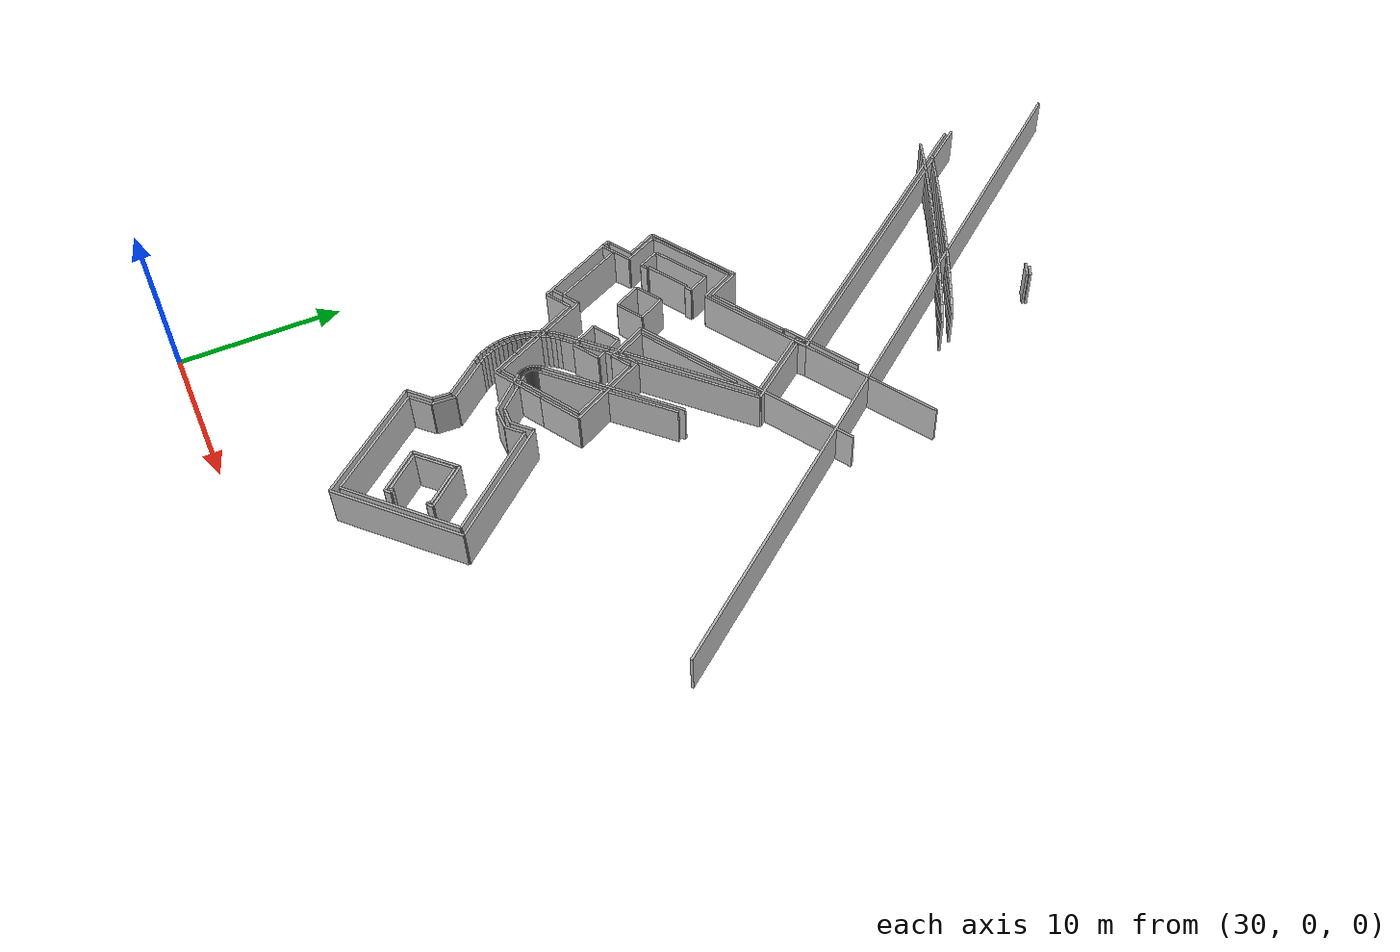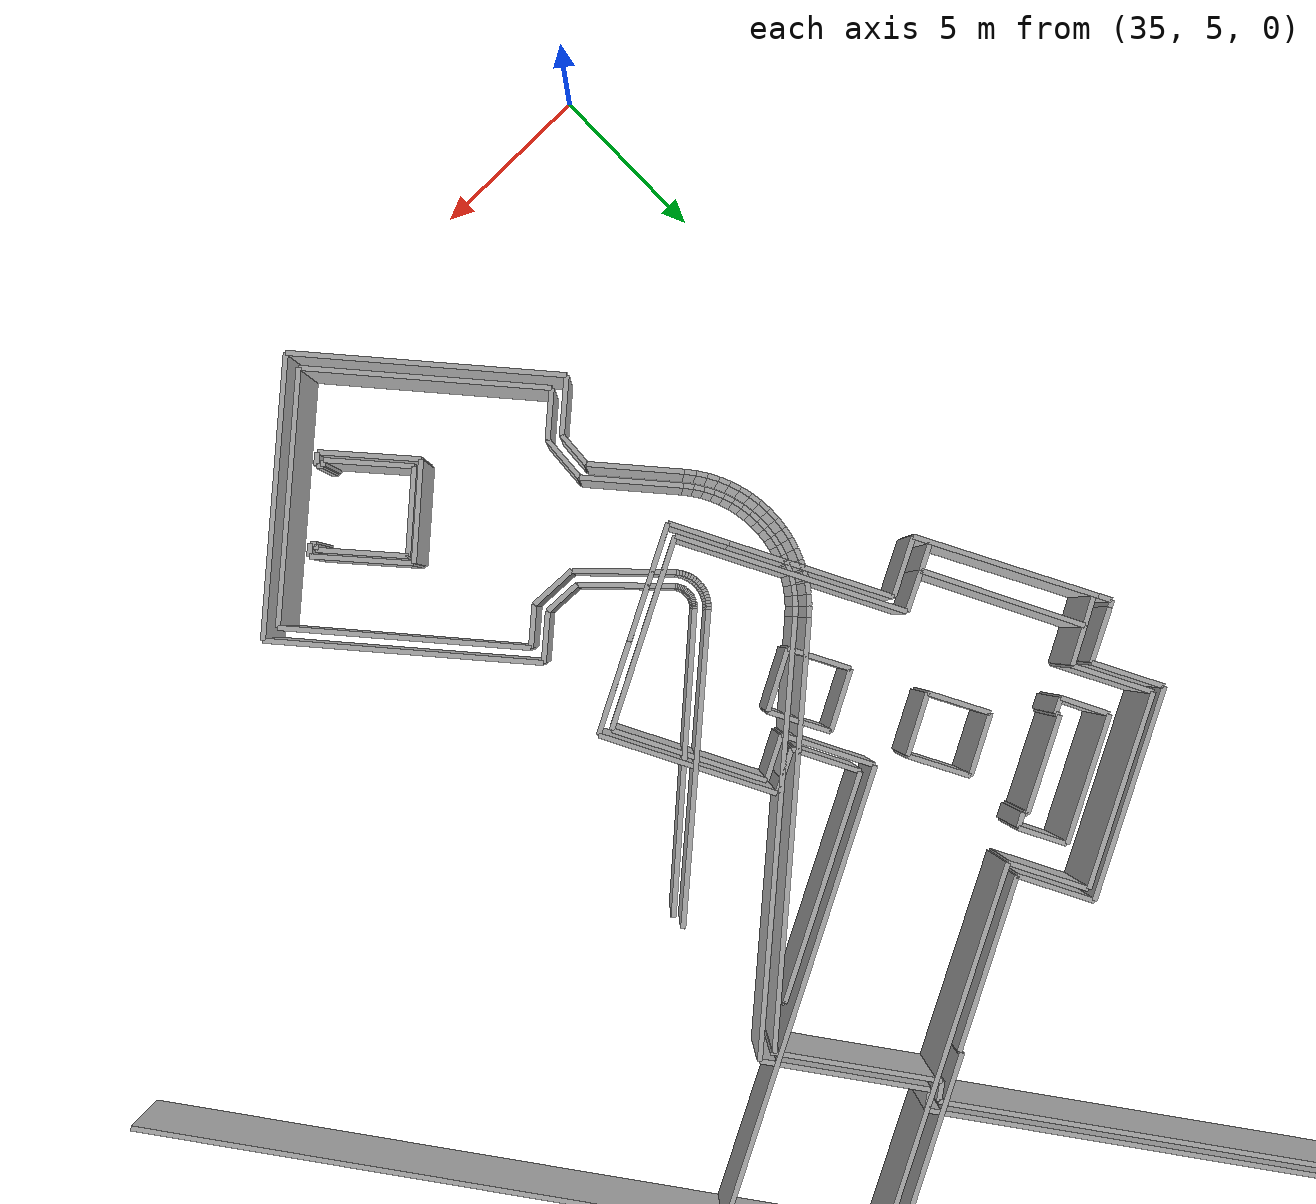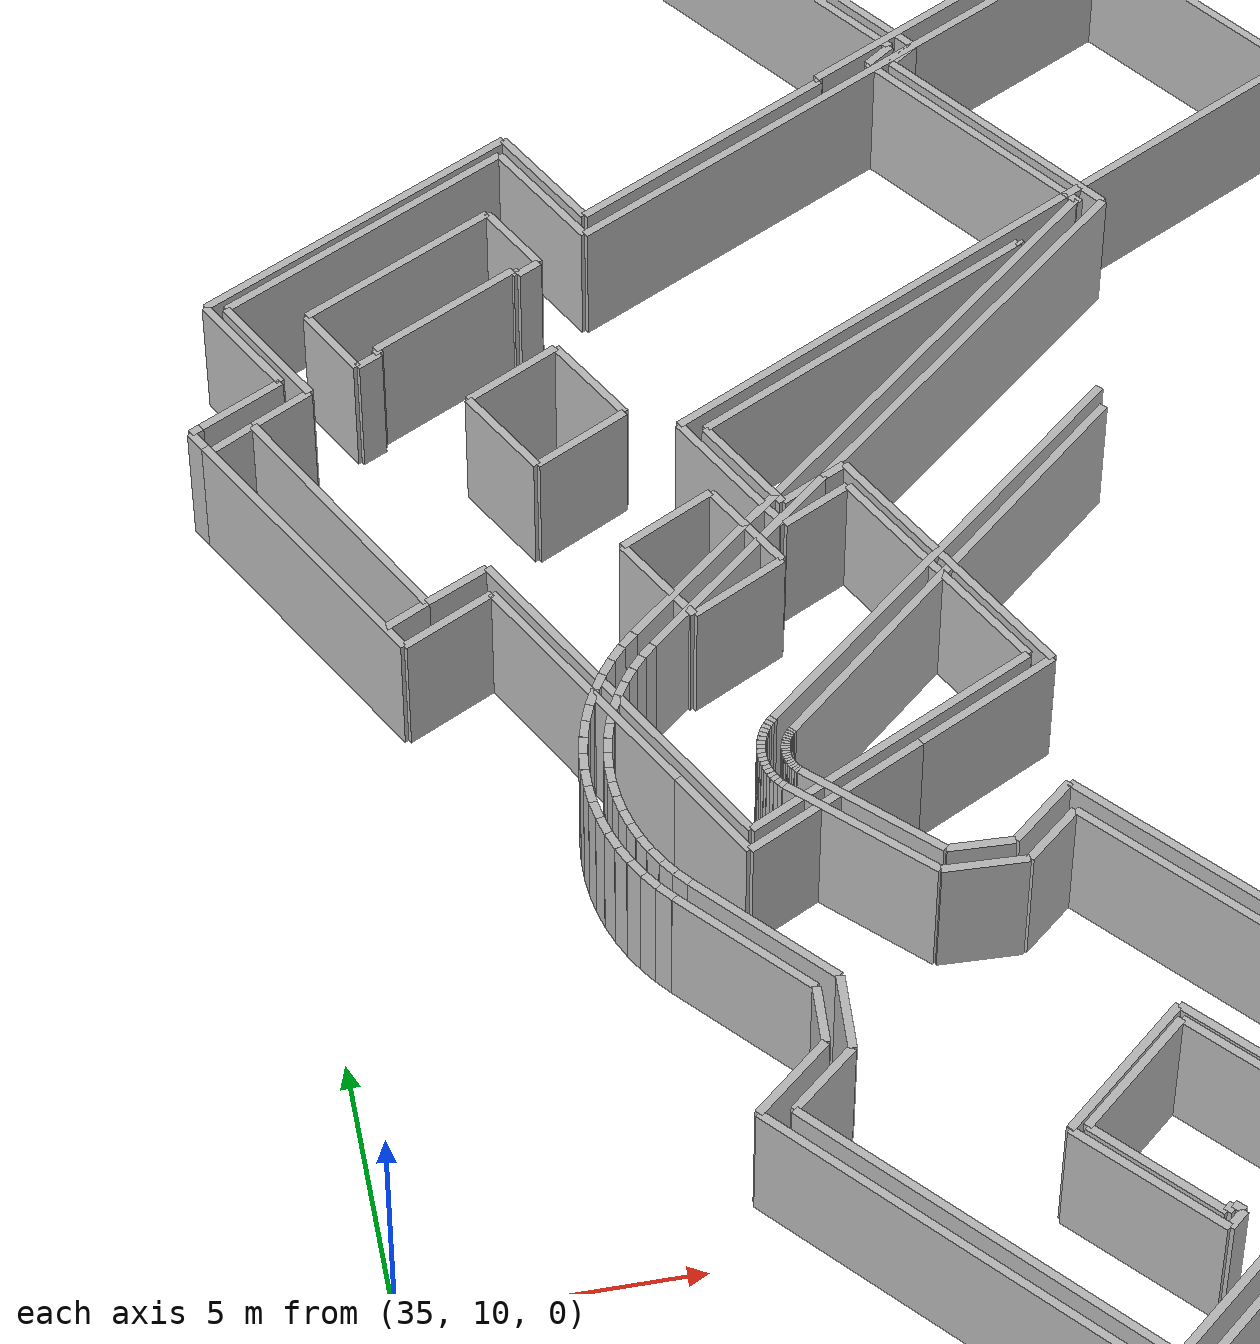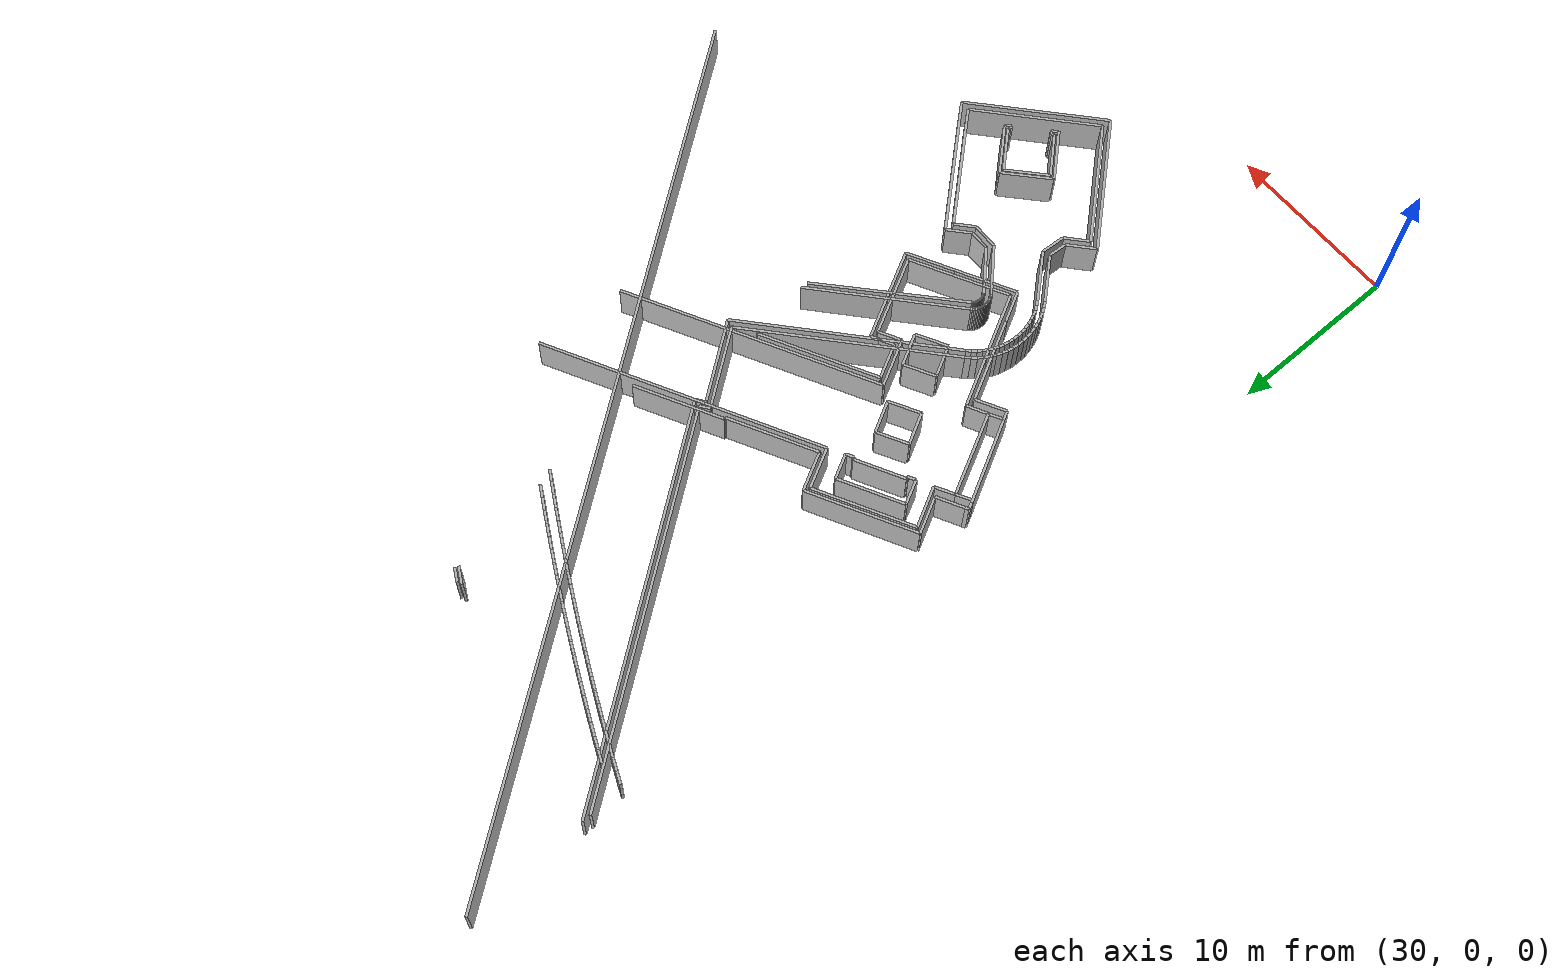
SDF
<?xml version="1.0" ?>
<sdf version="1.6">
  <model name="sps_0505">
    <pose frame="">0 0 0 0 -0 0</pose>
    <static>1</static>
    <self_collide>0</self_collide>
    <allow_auto_disable>0</allow_auto_disable>
    <link name="Wall106">
      <kinematic>0</kinematic>
      <gravity>1</gravity>
      <self_collide>0</self_collide>
      <collision name="collision">
        <geometry>
          <box>
            <size>2.20003 0.15 2.5</size>
          </box>
        </geometry>
        <pose frame="">0 0 0 0 -0 0</pose>
      </collision>
      <visual name="visual">
        <geometry>
          <box>
            <size>2.20003 0.15 2.5</size>
          </box>
        </geometry>
        <pose frame="">0 0 0 0 -0 0</pose>
        <cast_shadows>1</cast_shadows>
        <transparency>0.0</transparency>
      </visual>
      <pose frame="">35.4419 28.5977 1.25 0 0 -1.08942</pose>
    </link>
    <link name="Wall108">
      <kinematic>0</kinematic>
      <gravity>1</gravity>
      <self_collide>0</self_collide>
      <collision name="collision">
        <geometry>
          <box>
            <size>2.08435 0.15 2.5</size>
          </box>
        </geometry>
        <pose frame="">0 0 0 0 -0 0</pose>
      </collision>
      <visual name="visual">
        <geometry>
          <box>
            <size>2.08435 0.15 2.5</size>
          </box>
        </geometry>
        <pose frame="">0 0 0 0 -0 0</pose>
        <cast_shadows>1</cast_shadows>
        <transparency>0.0</transparency>
      </visual>
      <pose frame="">43.3747 24.2935 1.25 0 -0 2.05206</pose>
    </link>
    <link name="Wall111">
      <kinematic>0</kinematic>
      <gravity>1</gravity>
      <self_collide>0</self_collide>
      <collision name="collision">
        <geometry>
          <box>
            <size>8.10007 0.15 2.5</size>
          </box>
        </geometry>
        <pose frame="">0 0 0 0 -0 0</pose>
      </collision>
      <visual name="visual">
        <geometry>
          <box>
            <size>8.10007 0.15 2.5</size>
          </box>
        </geometry>
        <pose frame="">0 0 0 0 -0 0</pose>
        <cast_shadows>1</cast_shadows>
        <transparency>0.0</transparency>
      </visual>
      <pose frame="">43.6384 8.1064 1.25 0 -0 2.28845</pose>
    </link>
    <link name="Wall112">
      <kinematic>0</kinematic>
      <gravity>1</gravity>
      <self_collide>0</self_collide>
      <collision name="collision">
        <geometry>
          <box>
            <size>0.600333 0.15 2.5</size>
          </box>
        </geometry>
        <pose frame="">0 0 0 0 -0 0</pose>
      </collision>
      <visual name="visual">
        <geometry>
          <box>
            <size>0.600333 0.15 2.5</size>
          </box>
        </geometry>
        <pose frame="">0 0 0 0 -0 0</pose>
        <cast_shadows>1</cast_shadows>
        <transparency>0.0</transparency>
      </visual>
      <pose frame="">48.0919 33.3364 1.25 0 -0 0.630284</pose>
    </link>
    <link name="Wall115">
      <kinematic>0</kinematic>
      <gravity>1</gravity>
      <self_collide>0</self_collide>
      <collision name="collision">
        <geometry>
          <box>
            <size>9.20194 0.15 2.5</size>
          </box>
        </geometry>
        <pose frame="">0 0 0 0 -0 0</pose>
      </collision>
      <visual name="visual">
        <geometry>
          <box>
            <size>9.20194 0.15 2.5</size>
          </box>
        </geometry>
        <pose frame="">0 0 0 0 -0 0</pose>
        <cast_shadows>1</cast_shadows>
        <transparency>0.0</transparency>
      </visual>
      <pose frame="">46.2363 21.8574 1.25 0 0 -2.42382</pose>
    </link>
    <link name="Wall116">
      <kinematic>0</kinematic>
      <gravity>1</gravity>
      <self_collide>0</self_collide>
      <collision name="collision">
        <geometry>
          <box>
            <size>12.8173 0.15 2.5</size>
          </box>
        </geometry>
        <pose frame="">0 0 0 0 -0 0</pose>
      </collision>
      <visual name="visual">
        <geometry>
          <box>
            <size>12.8173 0.15 2.5</size>
          </box>
        </geometry>
        <pose frame="">0 0 0 0 -0 0</pose>
        <cast_shadows>1</cast_shadows>
        <transparency>0.0</transparency>
      </visual>
      <pose frame="">45.9539 24.9295 1.25 0 -0 0.717764</pose>
    </link>
    <link name="Wall143">
      <kinematic>0</kinematic>
      <gravity>1</gravity>
      <self_collide>0</self_collide>
      <collision name="collision">
        <geometry>
          <box>
            <size>51.876 0.15 2.5</size>
          </box>
        </geometry>
        <pose frame="">0 0 0 0 -0 0</pose>
      </collision>
      <visual name="visual">
        <geometry>
          <box>
            <size>51.876 0.15 2.5</size>
          </box>
        </geometry>
        <pose frame="">0 0 0 0 -0 0</pose>
        <cast_shadows>1</cast_shadows>
        <transparency>0.0</transparency>
      </visual>
      <pose frame="">49.7676 38.8393 1.25 0 -0 2.2016</pose>
    </link>
    <link name="Wall491">
      <kinematic>0</kinematic>
      <gravity>1</gravity>
      <self_collide>0</self_collide>
      <collision name="collision">
        <geometry>
          <box>
            <size>4.96539 0.15 2.5</size>
          </box>
        </geometry>
        <pose frame="">0 0 0 0 -0 0</pose>
      </collision>
      <visual name="visual">
        <geometry>
          <box>
            <size>4.96539 0.15 2.5</size>
          </box>
        </geometry>
        <pose frame="">0 0 0 0 -0 0</pose>
        <cast_shadows>1</cast_shadows>
        <transparency>0.0</transparency>
      </visual>
      <pose frame="">39.8523 20.0937 1.25 0 0 -1.08945</pose>
    </link>
    <link name="Wall492">
      <kinematic>0</kinematic>
      <gravity>1</gravity>
      <self_collide>0</self_collide>
      <collision name="collision">
        <geometry>
          <box>
            <size>1.8674 0.15 2.5</size>
          </box>
        </geometry>
        <pose frame="">0 0 0 0 -0 0</pose>
      </collision>
      <visual name="visual">
        <geometry>
          <box>
            <size>1.8674 0.15 2.5</size>
          </box>
        </geometry>
        <pose frame="">0 0 0 0 -0 0</pose>
        <cast_shadows>1</cast_shadows>
        <transparency>0.0</transparency>
      </visual>
      <pose frame="">41.434 17.0655 1.25 0 0 -1.08945</pose>
    </link>
    <link name="Wall499">
      <kinematic>0</kinematic>
      <gravity>1</gravity>
      <self_collide>0</self_collide>
      <collision name="collision">
        <geometry>
          <box>
            <size>1.3478 0.15 2.5</size>
          </box>
        </geometry>
        <pose frame="">0 0 0 0 -0 0</pose>
      </collision>
      <visual name="visual">
        <geometry>
          <box>
            <size>1.3478 0.15 2.5</size>
          </box>
        </geometry>
        <pose frame="">0 0 0 0 -0 0</pose>
        <cast_shadows>1</cast_shadows>
        <transparency>0.0</transparency>
      </visual>
      <pose frame="">44.4545 23.6816 1.25 0 0 -2.66043</pose>
    </link>
    <link name="Wall500">
      <kinematic>0</kinematic>
      <gravity>1</gravity>
      <self_collide>0</self_collide>
      <collision name="collision">
        <geometry>
          <box>
            <size>5.39962 0.15 2.5</size>
          </box>
        </geometry>
        <pose frame="">0 0 0 0 -0 0</pose>
      </collision>
      <visual name="visual">
        <geometry>
          <box>
            <size>5.39962 0.15 2.5</size>
          </box>
        </geometry>
        <pose frame="">0 0 0 0 -0 0</pose>
        <cast_shadows>1</cast_shadows>
        <transparency>0.0</transparency>
      </visual>
      <pose frame="">46.3018 21.6005 1.25 0 -0 2.05217</pose>
    </link>
    <link name="Wall501">
      <kinematic>0</kinematic>
      <gravity>1</gravity>
      <self_collide>0</self_collide>
      <collision name="collision">
        <geometry>
          <box>
            <size>1.05047 0.15 2.5</size>
          </box>
        </geometry>
        <pose frame="">0 0 0 0 -0 0</pose>
      </collision>
      <visual name="visual">
        <geometry>
          <box>
            <size>1.05047 0.15 2.5</size>
          </box>
        </geometry>
        <pose frame="">0 0 0 0 -0 0</pose>
        <cast_shadows>1</cast_shadows>
        <transparency>0.0</transparency>
      </visual>
      <pose frame="">48.6182 49.0603 1.25 0 -0 2.63246</pose>
    </link>
    <link name="Wall504">
      <kinematic>0</kinematic>
      <gravity>1</gravity>
      <self_collide>0</self_collide>
      <collision name="collision">
        <geometry>
          <box>
            <size>7.29947 0.15 2.5</size>
          </box>
        </geometry>
        <pose frame="">0 0 0 0 -0 0</pose>
      </collision>
      <visual name="visual">
        <geometry>
          <box>
            <size>7.29947 0.15 2.5</size>
          </box>
        </geometry>
        <pose frame="">0 0 0 0 -0 0</pose>
        <cast_shadows>1</cast_shadows>
        <transparency>0.0</transparency>
      </visual>
      <pose frame="">49.5895 13.3021 1.25 0 0 -0.853083</pose>
    </link>
    <link name="Wall828">
      <kinematic>0</kinematic>
      <gravity>1</gravity>
      <self_collide>0</self_collide>
      <collision name="collision">
        <geometry>
          <box>
            <size>1.82711 0.15 2.5</size>
          </box>
        </geometry>
        <pose frame="">0 0 0 0 -0 0</pose>
      </collision>
      <visual name="visual">
        <geometry>
          <box>
            <size>1.82711 0.15 2.5</size>
          </box>
        </geometry>
        <pose frame="">0 0 0 0 -0 0</pose>
        <cast_shadows>1</cast_shadows>
        <transparency>0.0</transparency>
      </visual>
      <pose frame="">37.8931 21.8714 1.25 0 -0 0.481262</pose>
    </link>
    <link name="Wall835">
      <kinematic>0</kinematic>
      <gravity>1</gravity>
      <self_collide>0</self_collide>
      <collision name="collision">
        <geometry>
          <box>
            <size>1.73339 0.15 2.5</size>
          </box>
        </geometry>
        <pose frame="">0 0 0 0 -0 0</pose>
      </collision>
      <visual name="visual">
        <geometry>
          <box>
            <size>1.73339 0.15 2.5</size>
          </box>
        </geometry>
        <pose frame="">0 0 0 0 -0 0</pose>
        <cast_shadows>1</cast_shadows>
        <transparency>0.0</transparency>
      </visual>
      <pose frame="">41.6279 11.7276 1.25 0 -0 0.717873</pose>
    </link>
    <link name="Wall836">
      <kinematic>0</kinematic>
      <gravity>1</gravity>
      <self_collide>0</self_collide>
      <collision name="collision">
        <geometry>
          <box>
            <size>2.83453 0.15 2.5</size>
          </box>
        </geometry>
        <pose frame="">0 0 0 0 -0 0</pose>
      </collision>
      <visual name="visual">
        <geometry>
          <box>
            <size>2.83453 0.15 2.5</size>
          </box>
        </geometry>
        <pose frame="">0 0 0 0 -0 0</pose>
        <cast_shadows>1</cast_shadows>
        <transparency>0.0</transparency>
      </visual>
      <pose frame="">41.4219 14.4457 1.25 0 -0 2.28852</pose>
    </link>
    <link name="Wall837">
      <kinematic>0</kinematic>
      <gravity>1</gravity>
      <self_collide>0</self_collide>
      <collision name="collision">
        <geometry>
          <box>
            <size>1.14115 0.15 2.5</size>
          </box>
        </geometry>
        <pose frame="">0 0 0 0 -0 0</pose>
      </collision>
      <visual name="visual">
        <geometry>
          <box>
            <size>1.14115 0.15 2.5</size>
          </box>
        </geometry>
        <pose frame="">0 0 0 0 -0 0</pose>
        <cast_shadows>1</cast_shadows>
        <transparency>0.0</transparency>
      </visual>
      <pose frame="">45.5337 15.6559 1.25 0 0 -0.0368063</pose>
    </link>
    <link name="Wall838">
      <kinematic>0</kinematic>
      <gravity>1</gravity>
      <self_collide>0</self_collide>
      <collision name="collision">
        <geometry>
          <box>
            <size>0.800268 0.15 2.5</size>
          </box>
        </geometry>
        <pose frame="">0 0 0 0 -0 0</pose>
      </collision>
      <visual name="visual">
        <geometry>
          <box>
            <size>0.800268 0.15 2.5</size>
          </box>
        </geometry>
        <pose frame="">0 0 0 0 -0 0</pose>
        <cast_shadows>1</cast_shadows>
        <transparency>0.0</transparency>
      </visual>
      <pose frame="">48.7814 49.1981 1.25 0 -0 2.63315</pose>
    </link>
    <link name="Wall839">
      <kinematic>0</kinematic>
      <gravity>1</gravity>
      <self_collide>0</self_collide>
      <collision name="collision">
        <geometry>
          <box>
            <size>12.5516 0.15 2.5</size>
          </box>
        </geometry>
        <pose frame="">0 0 0 0 -0 0</pose>
      </collision>
      <visual name="visual">
        <geometry>
          <box>
            <size>12.5516 0.15 2.5</size>
          </box>
        </geometry>
        <pose frame="">0 0 0 0 -0 0</pose>
        <cast_shadows>1</cast_shadows>
        <transparency>0.0</transparency>
      </visual>
      <pose frame="">45.5907 25.1437 1.25 0 -0 0.717718</pose>
    </link>
    <link name="Wall842">
      <kinematic>0</kinematic>
      <gravity>1</gravity>
      <self_collide>0</self_collide>
      <collision name="collision">
        <geometry>
          <box>
            <size>8.30061 0.15 2.5</size>
          </box>
        </geometry>
        <pose frame="">0 0 0 0 -0 0</pose>
      </collision>
      <visual name="visual">
        <geometry>
          <box>
            <size>8.30061 0.15 2.5</size>
          </box>
        </geometry>
        <pose frame="">0 0 0 0 -0 0</pose>
        <cast_shadows>1</cast_shadows>
        <transparency>0.0</transparency>
      </visual>
      <pose frame="">49.4281 7.78511 1.25 0 0 -2.42379</pose>
    </link>
    <link name="Wall1236">
      <kinematic>0</kinematic>
      <gravity>1</gravity>
      <self_collide>0</self_collide>
      <collision name="collision">
        <geometry>
          <box>
            <size>1.20587 0.15 2.5</size>
          </box>
        </geometry>
        <pose frame="">0 0 0 0 -0 0</pose>
      </collision>
      <visual name="visual">
        <geometry>
          <box>
            <size>1.20587 0.15 2.5</size>
          </box>
        </geometry>
        <pose frame="">0 0 0 0 -0 0</pose>
        <cast_shadows>1</cast_shadows>
        <transparency>0.0</transparency>
      </visual>
      <pose frame="">35.8755 27.0092 1.25 0 -0 0.495909</pose>
    </link>
    <link name="Wall1237">
      <kinematic>0</kinematic>
      <gravity>1</gravity>
      <self_collide>0</self_collide>
      <collision name="collision">
        <geometry>
          <box>
            <size>0.410405 0.15 2.5</size>
          </box>
        </geometry>
        <pose frame="">0 0 0 0 -0 0</pose>
      </collision>
      <visual name="visual">
        <geometry>
          <box>
            <size>0.410405 0.15 2.5</size>
          </box>
        </geometry>
        <pose frame="">0 0 0 0 -0 0</pose>
        <cast_shadows>1</cast_shadows>
        <transparency>0.0</transparency>
      </visual>
      <pose frame="">34.3734 26.5673 1.25 0 0 -1.08392</pose>
    </link>
    <link name="Wall1238">
      <kinematic>0</kinematic>
      <gravity>1</gravity>
      <self_collide>0</self_collide>
      <collision name="collision">
        <geometry>
          <box>
            <size>5.58664 0.15 2.5</size>
          </box>
        </geometry>
        <pose frame="">0 0 0 0 -0 0</pose>
      </collision>
      <visual name="visual">
        <geometry>
          <box>
            <size>5.58664 0.15 2.5</size>
          </box>
        </geometry>
        <pose frame="">0 0 0 0 -0 0</pose>
        <cast_shadows>1</cast_shadows>
        <transparency>0.0</transparency>
      </visual>
      <pose frame="">35.7764 23.9172 1.25 0 0 -1.08392</pose>
    </link>
    <link name="Wall1240">
      <kinematic>0</kinematic>
      <gravity>1</gravity>
      <self_collide>0</self_collide>
      <collision name="collision">
        <geometry>
          <box>
            <size>2.34308 0.15 2.5</size>
          </box>
        </geometry>
        <pose frame="">0 0 0 0 -0 0</pose>
      </collision>
      <visual name="visual">
        <geometry>
          <box>
            <size>2.34308 0.15 2.5</size>
          </box>
        </geometry>
        <pose frame="">0 0 0 0 -0 0</pose>
        <cast_shadows>1</cast_shadows>
        <transparency>0.0</transparency>
      </visual>
      <pose frame="">41.227 31.5385 1.25 0 -0 2.05214</pose>
    </link>
    <link name="Wall1241">
      <kinematic>0</kinematic>
      <gravity>1</gravity>
      <self_collide>0</self_collide>
      <collision name="collision">
        <geometry>
          <box>
            <size>1.08287 0.15 2.5</size>
          </box>
        </geometry>
        <pose frame="">0 0 0 0 -0 0</pose>
      </collision>
      <visual name="visual">
        <geometry>
          <box>
            <size>1.08287 0.15 2.5</size>
          </box>
        </geometry>
        <pose frame="">0 0 0 0 -0 0</pose>
        <cast_shadows>1</cast_shadows>
        <transparency>0.0</transparency>
      </visual>
      <pose frame="">42.3173 12.8379 1.25 0 -0 1.50299</pose>
    </link>
    <link name="Wall1244">
      <kinematic>0</kinematic>
      <gravity>1</gravity>
      <self_collide>0</self_collide>
      <collision name="collision">
        <geometry>
          <box>
            <size>3.0084 0.15 2.5</size>
          </box>
        </geometry>
        <pose frame="">0 0 0 0 -0 0</pose>
      </collision>
      <visual name="visual">
        <geometry>
          <box>
            <size>3.0084 0.15 2.5</size>
          </box>
        </geometry>
        <pose frame="">0 0 0 0 -0 0</pose>
        <cast_shadows>1</cast_shadows>
        <transparency>0.0</transparency>
      </visual>
      <pose frame="">43.7328 16.3517 1.25 0 0 -0.790663</pose>
    </link>
    <link name="Wall1248">
      <kinematic>0</kinematic>
      <gravity>1</gravity>
      <self_collide>0</self_collide>
      <collision name="collision">
        <geometry>
          <box>
            <size>7.50063 0.15 2.5</size>
          </box>
        </geometry>
        <pose frame="">0 0 0 0 -0 0</pose>
      </collision>
      <visual name="visual">
        <geometry>
          <box>
            <size>7.50063 0.15 2.5</size>
          </box>
        </geometry>
        <pose frame="">0 0 0 0 -0 0</pose>
        <cast_shadows>1</cast_shadows>
        <transparency>0.0</transparency>
      </visual>
      <pose frame="">49.1646 8.08629 1.25 0 0 -2.4239</pose>
    </link>
    <link name="Wall1535">
      <kinematic>0</kinematic>
      <gravity>1</gravity>
      <self_collide>0</self_collide>
      <collision name="collision">
        <geometry>
          <box>
            <size>4.9612 0.15 2.5</size>
          </box>
        </geometry>
        <pose frame="">0 0 0 0 -0 0</pose>
      </collision>
      <visual name="visual">
        <geometry>
          <box>
            <size>4.9612 0.15 2.5</size>
          </box>
        </geometry>
        <pose frame="">0 0 0 0 -0 0</pose>
        <cast_shadows>1</cast_shadows>
        <transparency>0.0</transparency>
      </visual>
      <pose frame="">36.477 24.5149 1.25 0 0 -1.09705</pose>
    </link>
    <link name="Wall1538">
      <kinematic>0</kinematic>
      <gravity>1</gravity>
      <self_collide>0</self_collide>
      <collision name="collision">
        <geometry>
          <box>
            <size>1.45714 0.15 2.5</size>
          </box>
        </geometry>
        <pose frame="">0 0 0 0 -0 0</pose>
      </collision>
      <visual name="visual">
        <geometry>
          <box>
            <size>1.45714 0.15 2.5</size>
          </box>
        </geometry>
        <pose frame="">0 0 0 0 -0 0</pose>
        <cast_shadows>1</cast_shadows>
        <transparency>0.0</transparency>
      </visual>
      <pose frame="">45.5189 15.256 1.25 0 0 -0.0363659</pose>
    </link>
    <link name="Wall1539">
      <kinematic>0</kinematic>
      <gravity>1</gravity>
      <self_collide>0</self_collide>
      <collision name="collision">
        <geometry>
          <box>
            <size>7.29966 0.15 2.5</size>
          </box>
        </geometry>
        <pose frame="">0 0 0 0 -0 0</pose>
      </collision>
      <visual name="visual">
        <geometry>
          <box>
            <size>7.29966 0.15 2.5</size>
          </box>
        </geometry>
        <pose frame="">0 0 0 0 -0 0</pose>
        <cast_shadows>1</cast_shadows>
        <transparency>0.0</transparency>
      </visual>
      <pose frame="">43.9391 8.3694 1.25 0 -0 2.28849</pose>
    </link>
    <link name="Wall1540">
      <kinematic>0</kinematic>
      <gravity>1</gravity>
      <self_collide>0</self_collide>
      <collision name="collision">
        <geometry>
          <box>
            <size>5.27131 0.15 2.5</size>
          </box>
        </geometry>
        <pose frame="">0 0 0 0 -0 0</pose>
      </collision>
      <visual name="visual">
        <geometry>
          <box>
            <size>5.27131 0.15 2.5</size>
          </box>
        </geometry>
        <pose frame="">0 0 0 0 -0 0</pose>
        <cast_shadows>1</cast_shadows>
        <transparency>0.0</transparency>
      </visual>
      <pose frame="">48.7901 34.2599 1.25 0 0 -2.66026</pose>
    </link>
    <link name="Wall1544">
      <kinematic>0</kinematic>
      <gravity>1</gravity>
      <self_collide>0</self_collide>
      <collision name="collision">
        <geometry>
          <box>
            <size>15.156 0.15 2.5</size>
          </box>
        </geometry>
        <pose frame="">0 0 0 0 -0 0</pose>
      </collision>
      <visual name="visual">
        <geometry>
          <box>
            <size>15.156 0.15 2.5</size>
          </box>
        </geometry>
        <pose frame="">0 0 0 0 -0 0</pose>
        <cast_shadows>1</cast_shadows>
        <transparency>0.0</transparency>
      </visual>
      <pose frame="">49.1872 28.8946 1.25 0 -0 0.481298</pose>
    </link>
    <link name="Wall1840">
      <kinematic>0</kinematic>
      <gravity>1</gravity>
      <self_collide>0</self_collide>
      <collision name="collision">
        <geometry>
          <box>
            <size>0.931451 0.15 2.5</size>
          </box>
        </geometry>
        <pose frame="">0 0 0 0 -0 0</pose>
      </collision>
      <visual name="visual">
        <geometry>
          <box>
            <size>0.931451 0.15 2.5</size>
          </box>
        </geometry>
        <pose frame="">0 0 0 0 -0 0</pose>
        <cast_shadows>1</cast_shadows>
        <transparency>0.0</transparency>
      </visual>
      <pose frame="">34.9387 26.495 1.25 0 0 -2.63174</pose>
    </link>
    <link name="Wall1841">
      <kinematic>0</kinematic>
      <gravity>1</gravity>
      <self_collide>0</self_collide>
      <collision name="collision">
        <geometry>
          <box>
            <size>1.67167 0.15 2.5</size>
          </box>
        </geometry>
        <pose frame="">0 0 0 0 -0 0</pose>
      </collision>
      <visual name="visual">
        <geometry>
          <box>
            <size>1.67167 0.15 2.5</size>
          </box>
        </geometry>
        <pose frame="">0 0 0 0 -0 0</pose>
        <cast_shadows>1</cast_shadows>
        <transparency>0.0</transparency>
      </visual>
      <pose frame="">35.2103 27.2358 1.25 0 0 -2.66037</pose>
    </link>
    <link name="Wall1842">
      <kinematic>0</kinematic>
      <gravity>1</gravity>
      <self_collide>0</self_collide>
      <collision name="collision">
        <geometry>
          <box>
            <size>0.216618 0.15 2.5</size>
          </box>
        </geometry>
        <pose frame="">0 0 0 0 -0 0</pose>
      </collision>
      <visual name="visual">
        <geometry>
          <box>
            <size>0.216618 0.15 2.5</size>
          </box>
        </geometry>
        <pose frame="">0 0 0 0 -0 0</pose>
        <cast_shadows>1</cast_shadows>
        <transparency>0.0</transparency>
      </visual>
      <pose frame="">34.3734 26.7988 1.25 0 0 -2.66037</pose>
    </link>
    <link name="Wall1843">
      <kinematic>0</kinematic>
      <gravity>1</gravity>
      <self_collide>0</self_collide>
      <collision name="collision">
        <geometry>
          <box>
            <size>1.47797 0.15 2.5</size>
          </box>
        </geometry>
        <pose frame="">0 0 0 0 -0 0</pose>
      </collision>
      <visual name="visual">
        <geometry>
          <box>
            <size>1.47797 0.15 2.5</size>
          </box>
        </geometry>
        <pose frame="">0 0 0 0 -0 0</pose>
        <cast_shadows>1</cast_shadows>
        <transparency>0.0</transparency>
      </visual>
      <pose frame="">36.9553 28.3842 1.25 0 -0 2.04192</pose>
    </link>
    <link name="Wall1844">
      <kinematic>0</kinematic>
      <gravity>1</gravity>
      <self_collide>0</self_collide>
      <collision name="collision">
        <geometry>
          <box>
            <size>0.866235 0.15 2.5</size>
          </box>
        </geometry>
        <pose frame="">0 0 0 0 -0 0</pose>
      </collision>
      <visual name="visual">
        <geometry>
          <box>
            <size>0.866235 0.15 2.5</size>
          </box>
        </geometry>
        <pose frame="">0 0 0 0 -0 0</pose>
        <cast_shadows>1</cast_shadows>
        <transparency>0.0</transparency>
      </visual>
      <pose frame="">37.2258 22.1051 1.25 0 0 -2.65529</pose>
    </link>
    <link name="Wall1845">
      <kinematic>0</kinematic>
      <gravity>1</gravity>
      <self_collide>0</self_collide>
      <collision name="collision">
        <geometry>
          <box>
            <size>1.24537 0.15 2.5</size>
          </box>
        </geometry>
        <pose frame="">0 0 0 0 -0 0</pose>
      </collision>
      <visual name="visual">
        <geometry>
          <box>
            <size>1.24537 0.15 2.5</size>
          </box>
        </geometry>
        <pose frame="">0 0 0 0 -0 0</pose>
        <cast_shadows>1</cast_shadows>
        <transparency>0.0</transparency>
      </visual>
      <pose frame="">38.1655 22.5861 1.25 0 -0 0.463867</pose>
    </link>
    <link name="Wall1847">
      <kinematic>0</kinematic>
      <gravity>1</gravity>
      <self_collide>0</self_collide>
      <collision name="collision">
        <geometry>
          <box>
            <size>1.25034 0.15 2.5</size>
          </box>
        </geometry>
        <pose frame="">0 0 0 0 -0 0</pose>
      </collision>
      <visual name="visual">
        <geometry>
          <box>
            <size>1.25034 0.15 2.5</size>
          </box>
        </geometry>
        <pose frame="">0 0 0 0 -0 0</pose>
        <cast_shadows>1</cast_shadows>
        <transparency>0.0</transparency>
      </visual>
      <pose frame="">46.7181 15.6405 1.25 0 -0 0.717347</pose>
    </link>
    <link name="Wall1849">
      <kinematic>0</kinematic>
      <gravity>1</gravity>
      <self_collide>0</self_collide>
      <collision name="collision">
        <geometry>
          <box>
            <size>22.7968 0.15 2.5</size>
          </box>
        </geometry>
        <pose frame="">0 0 0 0 -0 0</pose>
      </collision>
      <visual name="visual">
        <geometry>
          <box>
            <size>22.7968 0.15 2.5</size>
          </box>
        </geometry>
        <pose frame="">0 0 0 0 -0 0</pose>
        <cast_shadows>1</cast_shadows>
        <transparency>0.0</transparency>
      </visual>
      <pose frame="">41.1923 42.7836 1.25 0 0 -0.939982</pose>
    </link>
    <link name="Wall1850">
      <kinematic>0</kinematic>
      <gravity>1</gravity>
      <self_collide>0</self_collide>
      <collision name="collision">
        <geometry>
          <box>
            <size>8.90177 0.15 2.5</size>
          </box>
        </geometry>
        <pose frame="">0 0 0 0 -0 0</pose>
      </collision>
      <visual name="visual">
        <geometry>
          <box>
            <size>8.90177 0.15 2.5</size>
          </box>
        </geometry>
        <pose frame="">0 0 0 0 -0 0</pose>
        <cast_shadows>1</cast_shadows>
        <transparency>0.0</transparency>
      </visual>
      <pose frame="">46.3534 21.4957 1.25 0 0 -2.41261</pose>
    </link>
    <link name="Wall1856">
      <kinematic>0</kinematic>
      <gravity>1</gravity>
      <self_collide>0</self_collide>
      <collision name="collision">
        <geometry>
          <box>
            <size>16.4819 0.15 2.5</size>
          </box>
        </geometry>
        <pose frame="">0 0 0 0 -0 0</pose>
      </collision>
      <visual name="visual">
        <geometry>
          <box>
            <size>16.4819 0.15 2.5</size>
          </box>
        </geometry>
        <pose frame="">0 0 0 0 -0 0</pose>
        <cast_shadows>1</cast_shadows>
        <transparency>0.0</transparency>
      </visual>
      <pose frame="">48.9984 33.8667 1.25 0 -0 0.480617</pose>
    </link>
    <link name="Wall2183">
      <kinematic>0</kinematic>
      <gravity>1</gravity>
      <self_collide>0</self_collide>
      <collision name="collision">
        <geometry>
          <box>
            <size>6.4893 0.15 2.5</size>
          </box>
        </geometry>
        <pose frame="">0 0 0 0 -0 0</pose>
      </collision>
      <visual name="visual">
        <geometry>
          <box>
            <size>6.4893 0.15 2.5</size>
          </box>
        </geometry>
        <pose frame="">0 0 0 0 -0 0</pose>
        <cast_shadows>1</cast_shadows>
        <transparency>0.0</transparency>
      </visual>
      <pose frame="">37.8086 31.0748 1.25 0 0 -2.66027</pose>
    </link>
    <link name="Wall2184">
      <kinematic>0</kinematic>
      <gravity>1</gravity>
      <self_collide>0</self_collide>
      <collision name="collision">
        <geometry>
          <box>
            <size>3.00035 0.15 2.5</size>
          </box>
        </geometry>
        <pose frame="">0 0 0 0 -0 0</pose>
      </collision>
      <visual name="visual">
        <geometry>
          <box>
            <size>3.00035 0.15 2.5</size>
          </box>
        </geometry>
        <pose frame="">0 0 0 0 -0 0</pose>
        <cast_shadows>1</cast_shadows>
        <transparency>0.0</transparency>
      </visual>
      <pose frame="">41.7782 14.6467 1.25 0 -0 2.28842</pose>
    </link>
    <link name="Wall2185">
      <kinematic>0</kinematic>
      <gravity>1</gravity>
      <self_collide>0</self_collide>
      <collision name="collision">
        <geometry>
          <box>
            <size>2.82436 0.15 2.5</size>
          </box>
        </geometry>
        <pose frame="">0 0 0 0 -0 0</pose>
      </collision>
      <visual name="visual">
        <geometry>
          <box>
            <size>2.82436 0.15 2.5</size>
          </box>
        </geometry>
        <pose frame="">0 0 0 0 -0 0</pose>
        <cast_shadows>1</cast_shadows>
        <transparency>0.0</transparency>
      </visual>
      <pose frame="">43.9697 16.6803 1.25 0 0 -0.790242</pose>
    </link>
    <link name="Wall2186">
      <kinematic>0</kinematic>
      <gravity>1</gravity>
      <self_collide>0</self_collide>
      <collision name="collision">
        <geometry>
          <box>
            <size>0.0823129 0.15 2.5</size>
          </box>
        </geometry>
        <pose frame="">0 0 0 0 -0 0</pose>
      </collision>
      <visual name="visual">
        <geometry>
          <box>
            <size>0.0823129 0.15 2.5</size>
          </box>
        </geometry>
        <pose frame="">0 0 0 0 -0 0</pose>
        <cast_shadows>1</cast_shadows>
        <transparency>0.0</transparency>
      </visual>
      <pose frame="">46.4735 33.0035 1.25 0 0 -1.07465</pose>
    </link>
    <link name="Wall2187">
      <kinematic>0</kinematic>
      <gravity>1</gravity>
      <self_collide>0</self_collide>
      <collision name="collision">
        <geometry>
          <box>
            <size>0.600149 0.15 2.5</size>
          </box>
        </geometry>
        <pose frame="">0 0 0 0 -0 0</pose>
      </collision>
      <visual name="visual">
        <geometry>
          <box>
            <size>0.600149 0.15 2.5</size>
          </box>
        </geometry>
        <pose frame="">0 0 0 0 -0 0</pose>
        <cast_shadows>1</cast_shadows>
        <transparency>0.0</transparency>
      </visual>
      <pose frame="">47.6727 33.402 1.25 0 0 -2.51121</pose>
    </link>
    <link name="Wall2189">
      <kinematic>0</kinematic>
      <gravity>1</gravity>
      <self_collide>0</self_collide>
      <collision name="collision">
        <geometry>
          <box>
            <size>23.5069 0.15 2.5</size>
          </box>
        </geometry>
        <pose frame="">0 0 0 0 -0 0</pose>
      </collision>
      <visual name="visual">
        <geometry>
          <box>
            <size>23.5069 0.15 2.5</size>
          </box>
        </geometry>
        <pose frame="">0 0 0 0 -0 0</pose>
        <cast_shadows>1</cast_shadows>
        <transparency>0.0</transparency>
      </visual>
      <pose frame="">41.4019 43.0046 1.25 0 0 -0.939954</pose>
    </link>
    <link name="Wall2190">
      <kinematic>0</kinematic>
      <gravity>1</gravity>
      <self_collide>0</self_collide>
      <collision name="collision">
        <geometry>
          <box>
            <size>0.0598912 0.15 2.5</size>
          </box>
        </geometry>
        <pose frame="">0 0 0 0 -0 0</pose>
      </collision>
      <visual name="visual">
        <geometry>
          <box>
            <size>0.0598912 0.15 2.5</size>
          </box>
        </geometry>
        <pose frame="">0 0 0 0 -0 0</pose>
        <cast_shadows>1</cast_shadows>
        <transparency>0.0</transparency>
      </visual>
      <pose frame="">49.1197 28.4356 1.25 0 0 -1.04558</pose>
    </link>
    <link name="Wall2193">
      <kinematic>0</kinematic>
      <gravity>1</gravity>
      <self_collide>0</self_collide>
      <collision name="collision">
        <geometry>
          <box>
            <size>4.97162 0.15 2.5</size>
          </box>
        </geometry>
        <pose frame="">0 0 0 0 -0 0</pose>
      </collision>
      <visual name="visual">
        <geometry>
          <box>
            <size>4.97162 0.15 2.5</size>
          </box>
        </geometry>
        <pose frame="">0 0 0 0 -0 0</pose>
        <cast_shadows>1</cast_shadows>
        <transparency>0.0</transparency>
      </visual>
      <pose frame="">49.3155 31.152 1.25 0 -0 2.20154</pose>
    </link>
    <link name="Wall2571">
      <kinematic>0</kinematic>
      <gravity>1</gravity>
      <self_collide>0</self_collide>
      <collision name="collision">
        <geometry>
          <box>
            <size>1.50062 0.15 2.5</size>
          </box>
        </geometry>
        <pose frame="">0 0 0 0 -0 0</pose>
      </collision>
      <visual name="visual">
        <geometry>
          <box>
            <size>1.50062 0.15 2.5</size>
          </box>
        </geometry>
        <pose frame="">0 0 0 0 -0 0</pose>
        <cast_shadows>1</cast_shadows>
        <transparency>0.0</transparency>
      </visual>
      <pose frame="">42.1039 11.6125 1.25 0 -0 0.717961</pose>
    </link>
    <link name="Wall2572">
      <kinematic>0</kinematic>
      <gravity>1</gravity>
      <self_collide>0</self_collide>
      <collision name="collision">
        <geometry>
          <box>
            <size>1.41364 0.15 2.5</size>
          </box>
        </geometry>
        <pose frame="">0 0 0 0 -0 0</pose>
      </collision>
      <visual name="visual">
        <geometry>
          <box>
            <size>1.41364 0.15 2.5</size>
          </box>
        </geometry>
        <pose frame="">0 0 0 0 -0 0</pose>
        <cast_shadows>1</cast_shadows>
        <transparency>0.0</transparency>
      </visual>
      <pose frame="">42.7168 12.8113 1.25 0 -0 1.50309</pose>
    </link>
    <link name="Wall2573">
      <kinematic>0</kinematic>
      <gravity>1</gravity>
      <self_collide>0</self_collide>
      <collision name="collision">
        <geometry>
          <box>
            <size>5.32916 0.15 2.5</size>
          </box>
        </geometry>
        <pose frame="">0 0 0 0 -0 0</pose>
      </collision>
      <visual name="visual">
        <geometry>
          <box>
            <size>5.32916 0.15 2.5</size>
          </box>
        </geometry>
        <pose frame="">0 0 0 0 -0 0</pose>
        <cast_shadows>1</cast_shadows>
        <transparency>0.0</transparency>
      </visual>
      <pose frame="">44.1312 31.7337 1.25 0 0 -2.66025</pose>
    </link>
    <link name="Wall2574">
      <kinematic>0</kinematic>
      <gravity>1</gravity>
      <self_collide>0</self_collide>
      <collision name="collision">
        <geometry>
          <box>
            <size>1.49144 0.15 2.5</size>
          </box>
        </geometry>
        <pose frame="">0 0 0 0 -0 0</pose>
      </collision>
      <visual name="visual">
        <geometry>
          <box>
            <size>1.49144 0.15 2.5</size>
          </box>
        </geometry>
        <pose frame="">0 0 0 0 -0 0</pose>
        <cast_shadows>1</cast_shadows>
        <transparency>0.0</transparency>
      </visual>
      <pose frame="">46.6655 16.1255 1.25 0 -0 0.71801</pose>
    </link>
    <link name="Wall2575">
      <kinematic>0</kinematic>
      <gravity>1</gravity>
      <self_collide>0</self_collide>
      <collision name="collision">
        <geometry>
          <box>
            <size>3.5753 0.15 2.5</size>
          </box>
        </geometry>
        <pose frame="">0 0 0 0 -0 0</pose>
      </collision>
      <visual name="visual">
        <geometry>
          <box>
            <size>3.5753 0.15 2.5</size>
          </box>
        </geometry>
        <pose frame="">0 0 0 0 -0 0</pose>
        <cast_shadows>1</cast_shadows>
        <transparency>0.0</transparency>
      </visual>
      <pose frame="">43.4508 17.0655 1.25 0 -0 0.48133</pose>
    </link>
    <link name="Wall2576">
      <kinematic>0</kinematic>
      <gravity>1</gravity>
      <self_collide>0</self_collide>
      <collision name="collision">
        <geometry>
          <box>
            <size>2.83912 0.15 2.5</size>
          </box>
        </geometry>
        <pose frame="">0 0 0 0 -0 0</pose>
      </collision>
      <visual name="visual">
        <geometry>
          <box>
            <size>2.83912 0.15 2.5</size>
          </box>
        </geometry>
        <pose frame="">0 0 0 0 -0 0</pose>
        <cast_shadows>1</cast_shadows>
        <transparency>0.0</transparency>
      </visual>
      <pose frame="">46.2936 18.5503 1.25 0 -0 0.48133</pose>
    </link>
    <link name="Wall2577">
      <kinematic>0</kinematic>
      <gravity>1</gravity>
      <self_collide>0</self_collide>
      <collision name="collision">
        <geometry>
          <box>
            <size>7.00848 0.15 2.5</size>
          </box>
        </geometry>
        <pose frame="">0 0 0 0 -0 0</pose>
      </collision>
      <visual name="visual">
        <geometry>
          <box>
            <size>7.00848 0.15 2.5</size>
          </box>
        </geometry>
        <pose frame="">0 0 0 0 -0 0</pose>
        <cast_shadows>1</cast_shadows>
        <transparency>0.0</transparency>
      </visual>
      <pose frame="">45.9984 26.8394 1.25 0 -0 0.48126</pose>
    </link>
    <link name="Wall2578">
      <kinematic>0</kinematic>
      <gravity>1</gravity>
      <self_collide>0</self_collide>
      <collision name="collision">
        <geometry>
          <box>
            <size>4.99699 0.15 2.5</size>
          </box>
        </geometry>
        <pose frame="">0 0 0 0 -0 0</pose>
      </collision>
      <visual name="visual">
        <geometry>
          <box>
            <size>4.99699 0.15 2.5</size>
          </box>
        </geometry>
        <pose frame="">0 0 0 0 -0 0</pose>
        <cast_shadows>1</cast_shadows>
        <transparency>0.0</transparency>
      </visual>
      <pose frame="">48.9036 31.2073 1.25 0 0 -0.940096</pose>
    </link>
    <link name="Wall2579">
      <kinematic>0</kinematic>
      <gravity>1</gravity>
      <self_collide>0</self_collide>
      <collision name="collision">
        <geometry>
          <box>
            <size>5.27131 0.15 2.5</size>
          </box>
        </geometry>
        <pose frame="">0 0 0 0 -0 0</pose>
      </collision>
      <visual name="visual">
        <geometry>
          <box>
            <size>5.27131 0.15 2.5</size>
          </box>
        </geometry>
        <pose frame="">0 0 0 0 -0 0</pose>
        <cast_shadows>1</cast_shadows>
        <transparency>0.0</transparency>
      </visual>
      <pose frame="">48.7901 34.2599 1.25 0 0 -2.66026</pose>
    </link>
    <link name="Wall2580">
      <kinematic>0</kinematic>
      <gravity>1</gravity>
      <self_collide>0</self_collide>
      <collision name="collision">
        <geometry>
          <box>
            <size>8.09961 0.15 2.5</size>
          </box>
        </geometry>
        <pose frame="">0 0 0 0 -0 0</pose>
      </collision>
      <visual name="visual">
        <geometry>
          <box>
            <size>8.09961 0.15 2.5</size>
          </box>
        </geometry>
        <pose frame="">0 0 0 0 -0 0</pose>
        <cast_shadows>1</cast_shadows>
        <transparency>0.0</transparency>
      </visual>
      <pose frame="">49.8907 13.5655 1.25 0 0 -0.85302</pose>
    </link>
    <link name="Wall6908">
      <kinematic>0</kinematic>
      <gravity>1</gravity>
      <self_collide>0</self_collide>
      <collision name="collision">
        <geometry>
          <box>
            <size>3.92629 0.15 2.5</size>
          </box>
        </geometry>
        <pose frame="">0 0 0 0 -0 0</pose>
      </collision>
      <visual name="visual">
        <geometry>
          <box>
            <size>3.92629 0.15 2.5</size>
          </box>
        </geometry>
        <pose frame="">0 0 0 0 -0 0</pose>
        <cast_shadows>1</cast_shadows>
        <transparency>0.0</transparency>
      </visual>
      <pose frame="">38.3599 29.9517 1.25 0 -0 0.481411</pose>
    </link>
    <link name="Wall6909">
      <kinematic>0</kinematic>
      <gravity>1</gravity>
      <self_collide>0</self_collide>
      <collision name="collision">
        <geometry>
          <box>
            <size>1.48354 0.15 2.5</size>
          </box>
        </geometry>
        <pose frame="">0 0 0 0 -0 0</pose>
      </collision>
      <visual name="visual">
        <geometry>
          <box>
            <size>1.48354 0.15 2.5</size>
          </box>
        </geometry>
        <pose frame="">0 0 0 0 -0 0</pose>
        <cast_shadows>1</cast_shadows>
        <transparency>0.0</transparency>
      </visual>
      <pose frame="">40.4433 30.2032 1.25 0 0 -1.0895</pose>
    </link>
    <link name="Wall6910">
      <kinematic>0</kinematic>
      <gravity>1</gravity>
      <self_collide>0</self_collide>
      <collision name="collision">
        <geometry>
          <box>
            <size>0.468034 0.15 2.5</size>
          </box>
        </geometry>
        <pose frame="">0 0 0 0 -0 0</pose>
      </collision>
      <visual name="visual">
        <geometry>
          <box>
            <size>0.468034 0.15 2.5</size>
          </box>
        </geometry>
        <pose frame="">0 0 0 0 -0 0</pose>
        <cast_shadows>1</cast_shadows>
        <transparency>0.0</transparency>
      </visual>
      <pose frame="">40.5792 29.4373 1.25 0 0 -2.65998</pose>
    </link>
    <link name="Wall6911">
      <kinematic>0</kinematic>
      <gravity>1</gravity>
      <self_collide>0</self_collide>
      <collision name="collision">
        <geometry>
          <box>
            <size>0.130165 0.15 2.5</size>
          </box>
        </geometry>
        <pose frame="">0 0 0 0 -0 0</pose>
      </collision>
      <visual name="visual">
        <geometry>
          <box>
            <size>0.130165 0.15 2.5</size>
          </box>
        </geometry>
        <pose frame="">0 0 0 0 -0 0</pose>
        <cast_shadows>1</cast_shadows>
        <transparency>0.0</transparency>
      </visual>
      <pose frame="">40.3418 29.3866 1.25 0 -0 2.05143</pose>
    </link>
    <link name="Wall6912">
      <kinematic>0</kinematic>
      <gravity>1</gravity>
      <self_collide>0</self_collide>
      <collision name="collision">
        <geometry>
          <box>
            <size>2.98804 0.15 2.5</size>
          </box>
        </geometry>
        <pose frame="">0 0 0 0 -0 0</pose>
      </collision>
      <visual name="visual">
        <geometry>
          <box>
            <size>2.98804 0.15 2.5</size>
          </box>
        </geometry>
        <pose frame="">0 0 0 0 -0 0</pose>
        <cast_shadows>1</cast_shadows>
        <transparency>0.0</transparency>
      </visual>
      <pose frame="">38.9874 28.7527 1.25 0 0 -2.66032</pose>
    </link>
    <link name="Wall6913">
      <kinematic>0</kinematic>
      <gravity>1</gravity>
      <self_collide>0</self_collide>
      <collision name="collision">
        <geometry>
          <box>
            <size>0.124542 0.15 2.5</size>
          </box>
        </geometry>
        <pose frame="">0 0 0 0 -0 0</pose>
      </collision>
      <visual name="visual">
        <geometry>
          <box>
            <size>0.124542 0.15 2.5</size>
          </box>
        </geometry>
        <pose frame="">0 0 0 0 -0 0</pose>
        <cast_shadows>1</cast_shadows>
        <transparency>0.0</transparency>
      </visual>
      <pose frame="">37.6919 28.0059 1.25 0 0 -1.08983</pose>
    </link>
    <link name="Wall6914">
      <kinematic>0</kinematic>
      <gravity>1</gravity>
      <self_collide>0</self_collide>
      <collision name="collision">
        <geometry>
          <box>
            <size>0.485291 0.15 2.5</size>
          </box>
        </geometry>
        <pose frame="">0 0 0 0 -0 0</pose>
      </collision>
      <visual name="visual">
        <geometry>
          <box>
            <size>0.485291 0.15 2.5</size>
          </box>
        </geometry>
        <pose frame="">0 0 0 0 -0 0</pose>
        <cast_shadows>1</cast_shadows>
        <transparency>0.0</transparency>
      </visual>
      <pose frame="">37.5057 27.8382 1.25 0 0 -2.65955</pose>
    </link>
    <link name="Wall6915">
      <kinematic>0</kinematic>
      <gravity>1</gravity>
      <self_collide>0</self_collide>
      <collision name="collision">
        <geometry>
          <box>
            <size>0.340145 0.15 2.5</size>
          </box>
        </geometry>
        <pose frame="">0 0 0 0 -0 0</pose>
      </collision>
      <visual name="visual">
        <geometry>
          <box>
            <size>0.340145 0.15 2.5</size>
          </box>
        </geometry>
        <pose frame="">0 0 0 0 -0 0</pose>
        <cast_shadows>1</cast_shadows>
        <transparency>0.0</transparency>
      </visual>
      <pose frame="">40.3841 15.6465 1.25 0 -0 2.24201</pose>
    </link>
    <link name="Wall6916">
      <kinematic>0</kinematic>
      <gravity>1</gravity>
      <self_collide>0</self_collide>
      <collision name="collision">
        <geometry>
          <box>
            <size>0.339766 0.15 2.5</size>
          </box>
        </geometry>
        <pose frame="">0 0 0 0 -0 0</pose>
      </collision>
      <visual name="visual">
        <geometry>
          <box>
            <size>0.339766 0.15 2.5</size>
          </box>
        </geometry>
        <pose frame="">0 0 0 0 -0 0</pose>
        <cast_shadows>1</cast_shadows>
        <transparency>0.0</transparency>
      </visual>
      <pose frame="">40.1846 15.9214 1.25 0 -0 2.15516</pose>
    </link>
    <link name="Wall6917">
      <kinematic>0</kinematic>
      <gravity>1</gravity>
      <self_collide>0</self_collide>
      <collision name="collision">
        <geometry>
          <box>
            <size>0.339996 0.15 2.5</size>
          </box>
        </geometry>
        <pose frame="">0 0 0 0 -0 0</pose>
      </collision>
      <visual name="visual">
        <geometry>
          <box>
            <size>0.339996 0.15 2.5</size>
          </box>
        </geometry>
        <pose frame="">0 0 0 0 -0 0</pose>
        <cast_shadows>1</cast_shadows>
        <transparency>0.0</transparency>
      </visual>
      <pose frame="">40.0098 16.2125 1.25 0 -0 2.06801</pose>
    </link>
    <link name="Wall6918">
      <kinematic>0</kinematic>
      <gravity>1</gravity>
      <self_collide>0</self_collide>
      <collision name="collision">
        <geometry>
          <box>
            <size>0.340044 0.15 2.5</size>
          </box>
        </geometry>
        <pose frame="">0 0 0 0 -0 0</pose>
      </collision>
      <visual name="visual">
        <geometry>
          <box>
            <size>0.340044 0.15 2.5</size>
          </box>
        </geometry>
        <pose frame="">0 0 0 0 -0 0</pose>
        <cast_shadows>1</cast_shadows>
        <transparency>0.0</transparency>
      </visual>
      <pose frame="">39.8609 16.5178 1.25 0 -0 1.98104</pose>
    </link>
    <link name="Wall6919">
      <kinematic>0</kinematic>
      <gravity>1</gravity>
      <self_collide>0</self_collide>
      <collision name="collision">
        <geometry>
          <box>
            <size>0.340065 0.15 2.5</size>
          </box>
        </geometry>
        <pose frame="">0 0 0 0 -0 0</pose>
      </collision>
      <visual name="visual">
        <geometry>
          <box>
            <size>0.340065 0.15 2.5</size>
          </box>
        </geometry>
        <pose frame="">0 0 0 0 -0 0</pose>
        <cast_shadows>1</cast_shadows>
        <transparency>0.0</transparency>
      </visual>
      <pose frame="">39.7389 16.8349 1.25 0 -0 1.89465</pose>
    </link>
    <link name="Wall6920">
      <kinematic>0</kinematic>
      <gravity>1</gravity>
      <self_collide>0</self_collide>
      <collision name="collision">
        <geometry>
          <box>
            <size>0.339835 0.15 2.5</size>
          </box>
        </geometry>
        <pose frame="">0 0 0 0 -0 0</pose>
      </collision>
      <visual name="visual">
        <geometry>
          <box>
            <size>0.339835 0.15 2.5</size>
          </box>
        </geometry>
        <pose frame="">0 0 0 0 -0 0</pose>
        <cast_shadows>1</cast_shadows>
        <transparency>0.0</transparency>
      </visual>
      <pose frame="">39.645 17.1613 1.25 0 -0 1.80719</pose>
    </link>
    <link name="Wall6921">
      <kinematic>0</kinematic>
      <gravity>1</gravity>
      <self_collide>0</self_collide>
      <collision name="collision">
        <geometry>
          <box>
            <size>0.339968 0.15 2.5</size>
          </box>
        </geometry>
        <pose frame="">0 0 0 0 -0 0</pose>
      </collision>
      <visual name="visual">
        <geometry>
          <box>
            <size>0.339968 0.15 2.5</size>
          </box>
        </geometry>
        <pose frame="">0 0 0 0 -0 0</pose>
        <cast_shadows>1</cast_shadows>
        <transparency>0.0</transparency>
      </visual>
      <pose frame="">39.5799 17.4946 1.25 0 -0 1.72018</pose>
    </link>
    <link name="Wall6922">
      <kinematic>0</kinematic>
      <gravity>1</gravity>
      <self_collide>0</self_collide>
      <collision name="collision">
        <geometry>
          <box>
            <size>0.339909 0.15 2.5</size>
          </box>
        </geometry>
        <pose frame="">0 0 0 0 -0 0</pose>
      </collision>
      <visual name="visual">
        <geometry>
          <box>
            <size>0.339909 0.15 2.5</size>
          </box>
        </geometry>
        <pose frame="">0 0 0 0 -0 0</pose>
        <cast_shadows>1</cast_shadows>
        <transparency>0.0</transparency>
      </visual>
      <pose frame="">39.5439 17.8323 1.25 0 -0 1.63386</pose>
    </link>
    <link name="Wall6923">
      <kinematic>0</kinematic>
      <gravity>1</gravity>
      <self_collide>0</self_collide>
      <collision name="collision">
        <geometry>
          <box>
            <size>0.34007 0.15 2.5</size>
          </box>
        </geometry>
        <pose frame="">0 0 0 0 -0 0</pose>
      </collision>
      <visual name="visual">
        <geometry>
          <box>
            <size>0.34007 0.15 2.5</size>
          </box>
        </geometry>
        <pose frame="">0 0 0 0 -0 0</pose>
        <cast_shadows>1</cast_shadows>
        <transparency>0.0</transparency>
      </visual>
      <pose frame="">39.5374 18.1719 1.25 0 -0 1.54603</pose>
    </link>
    <link name="Wall6924">
      <kinematic>0</kinematic>
      <gravity>1</gravity>
      <self_collide>0</self_collide>
      <collision name="collision">
        <geometry>
          <box>
            <size>0.339915 0.15 2.5</size>
          </box>
        </geometry>
        <pose frame="">0 0 0 0 -0 0</pose>
      </collision>
      <visual name="visual">
        <geometry>
          <box>
            <size>0.339915 0.15 2.5</size>
          </box>
        </geometry>
        <pose frame="">0 0 0 0 -0 0</pose>
        <cast_shadows>1</cast_shadows>
        <transparency>0.0</transparency>
      </visual>
      <pose frame="">39.5604 18.5108 1.25 0 -0 1.45996</pose>
    </link>
    <link name="Wall6925">
      <kinematic>0</kinematic>
      <gravity>1</gravity>
      <self_collide>0</self_collide>
      <collision name="collision">
        <geometry>
          <box>
            <size>0.340043 0.15 2.5</size>
          </box>
        </geometry>
        <pose frame="">0 0 0 0 -0 0</pose>
      </collision>
      <visual name="visual">
        <geometry>
          <box>
            <size>0.340043 0.15 2.5</size>
          </box>
        </geometry>
        <pose frame="">0 0 0 0 -0 0</pose>
        <cast_shadows>1</cast_shadows>
        <transparency>0.0</transparency>
      </visual>
      <pose frame="">39.6128 18.8464 1.25 0 -0 1.37242</pose>
    </link>
    <link name="Wall6926">
      <kinematic>0</kinematic>
      <gravity>1</gravity>
      <self_collide>0</self_collide>
      <collision name="collision">
        <geometry>
          <box>
            <size>0.339947 0.15 2.5</size>
          </box>
        </geometry>
        <pose frame="">0 0 0 0 -0 0</pose>
      </collision>
      <visual name="visual">
        <geometry>
          <box>
            <size>0.339947 0.15 2.5</size>
          </box>
        </geometry>
        <pose frame="">0 0 0 0 -0 0</pose>
        <cast_shadows>1</cast_shadows>
        <transparency>0.0</transparency>
      </visual>
      <pose frame="">39.6941 19.1762 1.25 0 -0 1.28579</pose>
    </link>
    <link name="Wall6927">
      <kinematic>0</kinematic>
      <gravity>1</gravity>
      <self_collide>0</self_collide>
      <collision name="collision">
        <geometry>
          <box>
            <size>0.33986 0.15 2.5</size>
          </box>
        </geometry>
        <pose frame="">0 0 0 0 -0 0</pose>
      </collision>
      <visual name="visual">
        <geometry>
          <box>
            <size>0.33986 0.15 2.5</size>
          </box>
        </geometry>
        <pose frame="">0 0 0 0 -0 0</pose>
        <cast_shadows>1</cast_shadows>
        <transparency>0.0</transparency>
      </visual>
      <pose frame="">39.8036 19.4976 1.25 0 -0 1.19859</pose>
    </link>
    <link name="Wall6928">
      <kinematic>0</kinematic>
      <gravity>1</gravity>
      <self_collide>0</self_collide>
      <collision name="collision">
        <geometry>
          <box>
            <size>0.339891 0.15 2.5</size>
          </box>
        </geometry>
        <pose frame="">0 0 0 0 -0 0</pose>
      </collision>
      <visual name="visual">
        <geometry>
          <box>
            <size>0.339891 0.15 2.5</size>
          </box>
        </geometry>
        <pose frame="">0 0 0 0 -0 0</pose>
        <cast_shadows>1</cast_shadows>
        <transparency>0.0</transparency>
      </visual>
      <pose frame="">39.9406 19.8083 1.25 0 -0 1.11245</pose>
    </link>
    <link name="Wall6929">
      <kinematic>0</kinematic>
      <gravity>1</gravity>
      <self_collide>0</self_collide>
      <collision name="collision">
        <geometry>
          <box>
            <size>0.340061 0.15 2.5</size>
          </box>
        </geometry>
        <pose frame="">0 0 0 0 -0 0</pose>
      </collision>
      <visual name="visual">
        <geometry>
          <box>
            <size>0.340061 0.15 2.5</size>
          </box>
        </geometry>
        <pose frame="">0 0 0 0 -0 0</pose>
        <cast_shadows>1</cast_shadows>
        <transparency>0.0</transparency>
      </visual>
      <pose frame="">40.1041 20.106 1.25 0 -0 1.02462</pose>
    </link>
    <link name="Wall6930">
      <kinematic>0</kinematic>
      <gravity>1</gravity>
      <self_collide>0</self_collide>
      <collision name="collision">
        <geometry>
          <box>
            <size>0.339949 0.15 2.5</size>
          </box>
        </geometry>
        <pose frame="">0 0 0 0 -0 0</pose>
      </collision>
      <visual name="visual">
        <geometry>
          <box>
            <size>0.339949 0.15 2.5</size>
          </box>
        </geometry>
        <pose frame="">0 0 0 0 -0 0</pose>
        <cast_shadows>1</cast_shadows>
        <transparency>0.0</transparency>
      </visual>
      <pose frame="">40.293 20.3884 1.25 0 -0 0.938212</pose>
    </link>
    <link name="Wall6931">
      <kinematic>0</kinematic>
      <gravity>1</gravity>
      <self_collide>0</self_collide>
      <collision name="collision">
        <geometry>
          <box>
            <size>0.339995 0.15 2.5</size>
          </box>
        </geometry>
        <pose frame="">0 0 0 0 -0 0</pose>
      </collision>
      <visual name="visual">
        <geometry>
          <box>
            <size>0.339995 0.15 2.5</size>
          </box>
        </geometry>
        <pose frame="">0 0 0 0 -0 0</pose>
        <cast_shadows>1</cast_shadows>
        <transparency>0.0</transparency>
      </visual>
      <pose frame="">40.5055 20.6533 1.25 0 -0 0.850818</pose>
    </link>
    <link name="Wall6932">
      <kinematic>0</kinematic>
      <gravity>1</gravity>
      <self_collide>0</self_collide>
      <collision name="collision">
        <geometry>
          <box>
            <size>0.339949 0.15 2.5</size>
          </box>
        </geometry>
        <pose frame="">0 0 0 0 -0 0</pose>
      </collision>
      <visual name="visual">
        <geometry>
          <box>
            <size>0.339949 0.15 2.5</size>
          </box>
        </geometry>
        <pose frame="">0 0 0 0 -0 0</pose>
        <cast_shadows>1</cast_shadows>
        <transparency>0.0</transparency>
      </visual>
      <pose frame="">40.7403 20.8987 1.25 0 -0 0.764195</pose>
    </link>
    <link name="Wall6988">
      <kinematic>0</kinematic>
      <gravity>1</gravity>
      <self_collide>0</self_collide>
      <collision name="collision">
        <geometry>
          <box>
            <size>0.737416 0.15 2.5</size>
          </box>
        </geometry>
        <pose frame="">0 0 0 0 -0 0</pose>
      </collision>
      <visual name="visual">
        <geometry>
          <box>
            <size>0.737416 0.15 2.5</size>
          </box>
        </geometry>
        <pose frame="">0 0 0 0 -0 0</pose>
        <cast_shadows>1</cast_shadows>
        <transparency>0.0</transparency>
      </visual>
      <pose frame="">49.5656 42.9492 1.25 0 -0 2.61253</pose>
    </link>
    <link name="Wall6989">
      <kinematic>0</kinematic>
      <gravity>1</gravity>
      <self_collide>0</self_collide>
      <collision name="collision">
        <geometry>
          <box>
            <size>0.737245 0.15 2.5</size>
          </box>
        </geometry>
        <pose frame="">0 0 0 0 -0 0</pose>
      </collision>
      <visual name="visual">
        <geometry>
          <box>
            <size>0.737245 0.15 2.5</size>
          </box>
        </geometry>
        <pose frame="">0 0 0 0 -0 0</pose>
        <cast_shadows>1</cast_shadows>
        <transparency>0.0</transparency>
      </visual>
      <pose frame="">48.9282 43.3198 1.25 0 -0 2.61737</pose>
    </link>
    <link name="Wall6990">
      <kinematic>0</kinematic>
      <gravity>1</gravity>
      <self_collide>0</self_collide>
      <collision name="collision">
        <geometry>
          <box>
            <size>0.737327 0.15 2.5</size>
          </box>
        </geometry>
        <pose frame="">0 0 0 0 -0 0</pose>
      </collision>
      <visual name="visual">
        <geometry>
          <box>
            <size>0.737327 0.15 2.5</size>
          </box>
        </geometry>
        <pose frame="">0 0 0 0 -0 0</pose>
        <cast_shadows>1</cast_shadows>
        <transparency>0.0</transparency>
      </visual>
      <pose frame="">48.2889 43.6872 1.25 0 -0 2.6225</pose>
    </link>
    <link name="Wall6991">
      <kinematic>0</kinematic>
      <gravity>1</gravity>
      <self_collide>0</self_collide>
      <collision name="collision">
        <geometry>
          <box>
            <size>0.737368 0.15 2.5</size>
          </box>
        </geometry>
        <pose frame="">0 0 0 0 -0 0</pose>
      </collision>
      <visual name="visual">
        <geometry>
          <box>
            <size>0.737368 0.15 2.5</size>
          </box>
        </geometry>
        <pose frame="">0 0 0 0 -0 0</pose>
        <cast_shadows>1</cast_shadows>
        <transparency>0.0</transparency>
      </visual>
      <pose frame="">47.6478 44.0513 1.25 0 -0 2.62776</pose>
    </link>
    <link name="Wall6992">
      <kinematic>0</kinematic>
      <gravity>1</gravity>
      <self_collide>0</self_collide>
      <collision name="collision">
        <geometry>
          <box>
            <size>0.737222 0.15 2.5</size>
          </box>
        </geometry>
        <pose frame="">0 0 0 0 -0 0</pose>
      </collision>
      <visual name="visual">
        <geometry>
          <box>
            <size>0.737222 0.15 2.5</size>
          </box>
        </geometry>
        <pose frame="">0 0 0 0 -0 0</pose>
        <cast_shadows>1</cast_shadows>
        <transparency>0.0</transparency>
      </visual>
      <pose frame="">47.0048 44.4121 1.25 0 -0 2.63268</pose>
    </link>
    <link name="Wall6993">
      <kinematic>0</kinematic>
      <gravity>1</gravity>
      <self_collide>0</self_collide>
      <collision name="collision">
        <geometry>
          <box>
            <size>0.737238 0.15 2.5</size>
          </box>
        </geometry>
        <pose frame="">0 0 0 0 -0 0</pose>
      </collision>
      <visual name="visual">
        <geometry>
          <box>
            <size>0.737238 0.15 2.5</size>
          </box>
        </geometry>
        <pose frame="">0 0 0 0 -0 0</pose>
        <cast_shadows>1</cast_shadows>
        <transparency>0.0</transparency>
      </visual>
      <pose frame="">46.36 44.7695 1.25 0 -0 2.63828</pose>
    </link>
    <link name="Wall6994">
      <kinematic>0</kinematic>
      <gravity>1</gravity>
      <self_collide>0</self_collide>
      <collision name="collision">
        <geometry>
          <box>
            <size>0.73732 0.15 2.5</size>
          </box>
        </geometry>
        <pose frame="">0 0 0 0 -0 0</pose>
      </collision>
      <visual name="visual">
        <geometry>
          <box>
            <size>0.73732 0.15 2.5</size>
          </box>
        </geometry>
        <pose frame="">0 0 0 0 -0 0</pose>
        <cast_shadows>1</cast_shadows>
        <transparency>0.0</transparency>
      </visual>
      <pose frame="">45.7132 45.1235 1.25 0 -0 2.64325</pose>
    </link>
    <link name="Wall6995">
      <kinematic>0</kinematic>
      <gravity>1</gravity>
      <self_collide>0</self_collide>
      <collision name="collision">
        <geometry>
          <box>
            <size>0.737412 0.15 2.5</size>
          </box>
        </geometry>
        <pose frame="">0 0 0 0 -0 0</pose>
      </collision>
      <visual name="visual">
        <geometry>
          <box>
            <size>0.737412 0.15 2.5</size>
          </box>
        </geometry>
        <pose frame="">0 0 0 0 -0 0</pose>
        <cast_shadows>1</cast_shadows>
        <transparency>0.0</transparency>
      </visual>
      <pose frame="">45.0646 45.4742 1.25 0 -0 2.64859</pose>
    </link>
    <link name="Wall6996">
      <kinematic>0</kinematic>
      <gravity>1</gravity>
      <self_collide>0</self_collide>
      <collision name="collision">
        <geometry>
          <box>
            <size>0.737202 0.15 2.5</size>
          </box>
        </geometry>
        <pose frame="">0 0 0 0 -0 0</pose>
      </collision>
      <visual name="visual">
        <geometry>
          <box>
            <size>0.737202 0.15 2.5</size>
          </box>
        </geometry>
        <pose frame="">0 0 0 0 -0 0</pose>
        <cast_shadows>1</cast_shadows>
        <transparency>0.0</transparency>
      </visual>
      <pose frame="">44.4142 45.8215 1.25 0 -0 2.65369</pose>
    </link>
    <link name="Wall6997">
      <kinematic>0</kinematic>
      <gravity>1</gravity>
      <self_collide>0</self_collide>
      <collision name="collision">
        <geometry>
          <box>
            <size>0.737341 0.15 2.5</size>
          </box>
        </geometry>
        <pose frame="">0 0 0 0 -0 0</pose>
      </collision>
      <visual name="visual">
        <geometry>
          <box>
            <size>0.737341 0.15 2.5</size>
          </box>
        </geometry>
        <pose frame="">0 0 0 0 -0 0</pose>
        <cast_shadows>1</cast_shadows>
        <transparency>0.0</transparency>
      </visual>
      <pose frame="">43.7621 46.1655 1.25 0 -0 2.65866</pose>
    </link>
    <link name="Wall6998">
      <kinematic>0</kinematic>
      <gravity>1</gravity>
      <self_collide>0</self_collide>
      <collision name="collision">
        <geometry>
          <box>
            <size>0.737247 0.15 2.5</size>
          </box>
        </geometry>
        <pose frame="">0 0 0 0 -0 0</pose>
      </collision>
      <visual name="visual">
        <geometry>
          <box>
            <size>0.737247 0.15 2.5</size>
          </box>
        </geometry>
        <pose frame="">0 0 0 0 -0 0</pose>
        <cast_shadows>1</cast_shadows>
        <transparency>0.0</transparency>
      </visual>
      <pose frame="">43.1082 46.5061 1.25 0 -0 2.6641</pose>
    </link>
    <link name="Wall6999">
      <kinematic>0</kinematic>
      <gravity>1</gravity>
      <self_collide>0</self_collide>
      <collision name="collision">
        <geometry>
          <box>
            <size>0.737206 0.15 2.5</size>
          </box>
        </geometry>
        <pose frame="">0 0 0 0 -0 0</pose>
      </collision>
      <visual name="visual">
        <geometry>
          <box>
            <size>0.737206 0.15 2.5</size>
          </box>
        </geometry>
        <pose frame="">0 0 0 0 -0 0</pose>
        <cast_shadows>1</cast_shadows>
        <transparency>0.0</transparency>
      </visual>
      <pose frame="">42.4527 46.8433 1.25 0 -0 2.66891</pose>
    </link>
    <link name="Wall7000">
      <kinematic>0</kinematic>
      <gravity>1</gravity>
      <self_collide>0</self_collide>
      <collision name="collision">
        <geometry>
          <box>
            <size>0.737399 0.15 2.5</size>
          </box>
        </geometry>
        <pose frame="">0 0 0 0 -0 0</pose>
      </collision>
      <visual name="visual">
        <geometry>
          <box>
            <size>0.737399 0.15 2.5</size>
          </box>
        </geometry>
        <pose frame="">0 0 0 0 -0 0</pose>
        <cast_shadows>1</cast_shadows>
        <transparency>0.0</transparency>
      </visual>
      <pose frame="">41.7952 47.1771 1.25 0 -0 2.67461</pose>
    </link>
    <link name="Wall7001">
      <kinematic>0</kinematic>
      <gravity>1</gravity>
      <self_collide>0</self_collide>
      <collision name="collision">
        <geometry>
          <box>
            <size>0.737177 0.15 2.5</size>
          </box>
        </geometry>
        <pose frame="">0 0 0 0 -0 0</pose>
      </collision>
      <visual name="visual">
        <geometry>
          <box>
            <size>0.737177 0.15 2.5</size>
          </box>
        </geometry>
        <pose frame="">0 0 0 0 -0 0</pose>
        <cast_shadows>1</cast_shadows>
        <transparency>0.0</transparency>
      </visual>
      <pose frame="">41.1361 47.5075 1.25 0 -0 2.67928</pose>
    </link>
    <link name="Wall7002">
      <kinematic>0</kinematic>
      <gravity>1</gravity>
      <self_collide>0</self_collide>
      <collision name="collision">
        <geometry>
          <box>
            <size>0.737385 0.15 2.5</size>
          </box>
        </geometry>
        <pose frame="">0 0 0 0 -0 0</pose>
      </collision>
      <visual name="visual">
        <geometry>
          <box>
            <size>0.737385 0.15 2.5</size>
          </box>
        </geometry>
        <pose frame="">0 0 0 0 -0 0</pose>
        <cast_shadows>1</cast_shadows>
        <transparency>0.0</transparency>
      </visual>
      <pose frame="">40.4753 47.8345 1.25 0 -0 2.68487</pose>
    </link>
    <link name="Wall7003">
      <kinematic>0</kinematic>
      <gravity>1</gravity>
      <self_collide>0</self_collide>
      <collision name="collision">
        <geometry>
          <box>
            <size>0.737338 0.15 2.5</size>
          </box>
        </geometry>
        <pose frame="">0 0 0 0 -0 0</pose>
      </collision>
      <visual name="visual">
        <geometry>
          <box>
            <size>0.737338 0.15 2.5</size>
          </box>
        </geometry>
        <pose frame="">0 0 0 0 -0 0</pose>
        <cast_shadows>1</cast_shadows>
        <transparency>0.0</transparency>
      </visual>
      <pose frame="">39.8127 48.158 1.25 0 -0 2.6899</pose>
    </link>
    <link name="Wall7004">
      <kinematic>0</kinematic>
      <gravity>1</gravity>
      <self_collide>0</self_collide>
      <collision name="collision">
        <geometry>
          <box>
            <size>0.737257 0.15 2.5</size>
          </box>
        </geometry>
        <pose frame="">0 0 0 0 -0 0</pose>
      </collision>
      <visual name="visual">
        <geometry>
          <box>
            <size>0.737257 0.15 2.5</size>
          </box>
        </geometry>
        <pose frame="">0 0 0 0 -0 0</pose>
        <cast_shadows>1</cast_shadows>
        <transparency>0.0</transparency>
      </visual>
      <pose frame="">39.1486 48.4781 1.25 0 -0 2.69509</pose>
    </link>
    <link name="Wall7005">
      <kinematic>0</kinematic>
      <gravity>1</gravity>
      <self_collide>0</self_collide>
      <collision name="collision">
        <geometry>
          <box>
            <size>0.737304 0.15 2.5</size>
          </box>
        </geometry>
        <pose frame="">0 0 0 0 -0 0</pose>
      </collision>
      <visual name="visual">
        <geometry>
          <box>
            <size>0.737304 0.15 2.5</size>
          </box>
        </geometry>
        <pose frame="">0 0 0 0 -0 0</pose>
        <cast_shadows>1</cast_shadows>
        <transparency>0.0</transparency>
      </visual>
      <pose frame="">38.4827 48.7948 1.25 0 -0 2.70016</pose>
    </link>
    <link name="Wall7006">
      <kinematic>0</kinematic>
      <gravity>1</gravity>
      <self_collide>0</self_collide>
      <collision name="collision">
        <geometry>
          <box>
            <size>0.737454 0.15 2.5</size>
          </box>
        </geometry>
        <pose frame="">0 0 0 0 -0 0</pose>
      </collision>
      <visual name="visual">
        <geometry>
          <box>
            <size>0.737454 0.15 2.5</size>
          </box>
        </geometry>
        <pose frame="">0 0 0 0 -0 0</pose>
        <cast_shadows>1</cast_shadows>
        <transparency>0.0</transparency>
      </visual>
      <pose frame="">37.8152 49.1081 1.25 0 -0 2.70538</pose>
    </link>
    <link name="Wall7007">
      <kinematic>0</kinematic>
      <gravity>1</gravity>
      <self_collide>0</self_collide>
      <collision name="collision">
        <geometry>
          <box>
            <size>0.73724 0.15 2.5</size>
          </box>
        </geometry>
        <pose frame="">0 0 0 0 -0 0</pose>
      </collision>
      <visual name="visual">
        <geometry>
          <box>
            <size>0.73724 0.15 2.5</size>
          </box>
        </geometry>
        <pose frame="">0 0 0 0 -0 0</pose>
        <cast_shadows>1</cast_shadows>
        <transparency>0.0</transparency>
      </visual>
      <pose frame="">37.1461 49.4179 1.25 0 -0 2.71053</pose>
    </link>
    <link name="Wall7008">
      <kinematic>0</kinematic>
      <gravity>1</gravity>
      <self_collide>0</self_collide>
      <collision name="collision">
        <geometry>
          <box>
            <size>0.737238 0.15 2.5</size>
          </box>
        </geometry>
        <pose frame="">0 0 0 0 -0 0</pose>
      </collision>
      <visual name="visual">
        <geometry>
          <box>
            <size>0.737238 0.15 2.5</size>
          </box>
        </geometry>
        <pose frame="">0 0 0 0 -0 0</pose>
        <cast_shadows>1</cast_shadows>
        <transparency>0.0</transparency>
      </visual>
      <pose frame="">36.4755 49.7242 1.25 0 -0 2.71572</pose>
    </link>
    <link name="Wall9624">
      <kinematic>0</kinematic>
      <gravity>1</gravity>
      <self_collide>0</self_collide>
      <collision name="collision">
        <geometry>
          <box>
            <size>0.0522454 0.15 2.5</size>
          </box>
        </geometry>
        <pose frame="">0 0 0 0 -0 0</pose>
      </collision>
      <visual name="visual">
        <geometry>
          <box>
            <size>0.0522454 0.15 2.5</size>
          </box>
        </geometry>
        <pose frame="">0 0 0 0 -0 0</pose>
        <cast_shadows>1</cast_shadows>
        <transparency>0.0</transparency>
      </visual>
      <pose frame="">42.9597 17.7041 1.25 0 -0 2.24444</pose>
    </link>
    <link name="Wall9625">
      <kinematic>0</kinematic>
      <gravity>1</gravity>
      <self_collide>0</self_collide>
      <collision name="collision">
        <geometry>
          <box>
            <size>0.0523934 0.15 2.5</size>
          </box>
        </geometry>
        <pose frame="">0 0 0 0 -0 0</pose>
      </collision>
      <visual name="visual">
        <geometry>
          <box>
            <size>0.0523934 0.15 2.5</size>
          </box>
        </geometry>
        <pose frame="">0 0 0 0 -0 0</pose>
        <cast_shadows>1</cast_shadows>
        <transparency>0.0</transparency>
      </visual>
      <pose frame="">42.929 17.7464 1.25 0 -0 2.15298</pose>
    </link>
    <link name="Wall9626">
      <kinematic>0</kinematic>
      <gravity>1</gravity>
      <self_collide>0</self_collide>
      <collision name="collision">
        <geometry>
          <box>
            <size>0.0523551 0.15 2.5</size>
          </box>
        </geometry>
        <pose frame="">0 0 0 0 -0 0</pose>
      </collision>
      <visual name="visual">
        <geometry>
          <box>
            <size>0.0523551 0.15 2.5</size>
          </box>
        </geometry>
        <pose frame="">0 0 0 0 -0 0</pose>
        <cast_shadows>1</cast_shadows>
        <transparency>0.0</transparency>
      </visual>
      <pose frame="">42.9022 17.7913 1.25 0 -0 2.06782</pose>
    </link>
    <link name="Wall9627">
      <kinematic>0</kinematic>
      <gravity>1</gravity>
      <self_collide>0</self_collide>
      <collision name="collision">
        <geometry>
          <box>
            <size>0.0523499 0.15 2.5</size>
          </box>
        </geometry>
        <pose frame="">0 0 0 0 -0 0</pose>
      </collision>
      <visual name="visual">
        <geometry>
          <box>
            <size>0.0523499 0.15 2.5</size>
          </box>
        </geometry>
        <pose frame="">0 0 0 0 -0 0</pose>
        <cast_shadows>1</cast_shadows>
        <transparency>0.0</transparency>
      </visual>
      <pose frame="">42.8793 17.8383 1.25 0 -0 1.97967</pose>
    </link>
    <link name="Wall9628">
      <kinematic>0</kinematic>
      <gravity>1</gravity>
      <self_collide>0</self_collide>
      <collision name="collision">
        <geometry>
          <box>
            <size>0.0522672 0.15 2.5</size>
          </box>
        </geometry>
        <pose frame="">0 0 0 0 -0 0</pose>
      </collision>
      <visual name="visual">
        <geometry>
          <box>
            <size>0.0522672 0.15 2.5</size>
          </box>
        </geometry>
        <pose frame="">0 0 0 0 -0 0</pose>
        <cast_shadows>1</cast_shadows>
        <transparency>0.0</transparency>
      </visual>
      <pose frame="">42.8606 17.8871 1.25 0 -0 1.89402</pose>
    </link>
    <link name="Wall9629">
      <kinematic>0</kinematic>
      <gravity>1</gravity>
      <self_collide>0</self_collide>
      <collision name="collision">
        <geometry>
          <box>
            <size>0.0522872 0.15 2.5</size>
          </box>
        </geometry>
        <pose frame="">0 0 0 0 -0 0</pose>
      </collision>
      <visual name="visual">
        <geometry>
          <box>
            <size>0.0522872 0.15 2.5</size>
          </box>
        </geometry>
        <pose frame="">0 0 0 0 -0 0</pose>
        <cast_shadows>1</cast_shadows>
        <transparency>0.0</transparency>
      </visual>
      <pose frame="">42.8462 17.9373 1.25 0 -0 1.80643</pose>
    </link>
    <link name="Wall9630">
      <kinematic>0</kinematic>
      <gravity>1</gravity>
      <self_collide>0</self_collide>
      <collision name="collision">
        <geometry>
          <box>
            <size>0.0523441 0.15 2.5</size>
          </box>
        </geometry>
        <pose frame="">0 0 0 0 -0 0</pose>
      </collision>
      <visual name="visual">
        <geometry>
          <box>
            <size>0.0523441 0.15 2.5</size>
          </box>
        </geometry>
        <pose frame="">0 0 0 0 -0 0</pose>
        <cast_shadows>1</cast_shadows>
        <transparency>0.0</transparency>
      </visual>
      <pose frame="">42.8361 17.9886 1.25 0 -0 1.72061</pose>
    </link>
    <link name="Wall9631">
      <kinematic>0</kinematic>
      <gravity>1</gravity>
      <self_collide>0</self_collide>
      <collision name="collision">
        <geometry>
          <box>
            <size>0.0522929 0.15 2.5</size>
          </box>
        </geometry>
        <pose frame="">0 0 0 0 -0 0</pose>
      </collision>
      <visual name="visual">
        <geometry>
          <box>
            <size>0.0522929 0.15 2.5</size>
          </box>
        </geometry>
        <pose frame="">0 0 0 0 -0 0</pose>
        <cast_shadows>1</cast_shadows>
        <transparency>0.0</transparency>
      </visual>
      <pose frame="">42.8306 18.0406 1.25 0 -0 1.63504</pose>
    </link>
    <link name="Wall9632">
      <kinematic>0</kinematic>
      <gravity>1</gravity>
      <self_collide>0</self_collide>
      <collision name="collision">
        <geometry>
          <box>
            <size>0.052442 0.15 2.5</size>
          </box>
        </geometry>
        <pose frame="">0 0 0 0 -0 0</pose>
      </collision>
      <visual name="visual">
        <geometry>
          <box>
            <size>0.052442 0.15 2.5</size>
          </box>
        </geometry>
        <pose frame="">0 0 0 0 -0 0</pose>
        <cast_shadows>1</cast_shadows>
        <transparency>0.0</transparency>
      </visual>
      <pose frame="">42.8295 18.0929 1.25 0 -0 1.54868</pose>
    </link>
    <link name="Wall9633">
      <kinematic>0</kinematic>
      <gravity>1</gravity>
      <self_collide>0</self_collide>
      <collision name="collision">
        <geometry>
          <box>
            <size>0.0523518 0.15 2.5</size>
          </box>
        </geometry>
        <pose frame="">0 0 0 0 -0 0</pose>
      </collision>
      <visual name="visual">
        <geometry>
          <box>
            <size>0.0523518 0.15 2.5</size>
          </box>
        </geometry>
        <pose frame="">0 0 0 0 -0 0</pose>
        <cast_shadows>1</cast_shadows>
        <transparency>0.0</transparency>
      </visual>
      <pose frame="">42.8331 18.1451 1.25 0 -0 1.45512</pose>
    </link>
    <link name="Wall9634">
      <kinematic>0</kinematic>
      <gravity>1</gravity>
      <self_collide>0</self_collide>
      <collision name="collision">
        <geometry>
          <box>
            <size>0.0523927 0.15 2.5</size>
          </box>
        </geometry>
        <pose frame="">0 0 0 0 -0 0</pose>
      </collision>
      <visual name="visual">
        <geometry>
          <box>
            <size>0.0523927 0.15 2.5</size>
          </box>
        </geometry>
        <pose frame="">0 0 0 0 -0 0</pose>
        <cast_shadows>1</cast_shadows>
        <transparency>0.0</transparency>
      </visual>
      <pose frame="">42.8412 18.1968 1.25 0 -0 1.375</pose>
    </link>
    <link name="Wall9635">
      <kinematic>0</kinematic>
      <gravity>1</gravity>
      <self_collide>0</self_collide>
      <collision name="collision">
        <geometry>
          <box>
            <size>0.0523585 0.15 2.5</size>
          </box>
        </geometry>
        <pose frame="">0 0 0 0 -0 0</pose>
      </collision>
      <visual name="visual">
        <geometry>
          <box>
            <size>0.0523585 0.15 2.5</size>
          </box>
        </geometry>
        <pose frame="">0 0 0 0 -0 0</pose>
        <cast_shadows>1</cast_shadows>
        <transparency>0.0</transparency>
      </visual>
      <pose frame="">42.8537 18.2476 1.25 0 -0 1.28481</pose>
    </link>
    <link name="Wall9636">
      <kinematic>0</kinematic>
      <gravity>1</gravity>
      <self_collide>0</self_collide>
      <collision name="collision">
        <geometry>
          <box>
            <size>0.0523311 0.15 2.5</size>
          </box>
        </geometry>
        <pose frame="">0 0 0 0 -0 0</pose>
      </collision>
      <visual name="visual">
        <geometry>
          <box>
            <size>0.0523311 0.15 2.5</size>
          </box>
        </geometry>
        <pose frame="">0 0 0 0 -0 0</pose>
        <cast_shadows>1</cast_shadows>
        <transparency>0.0</transparency>
      </visual>
      <pose frame="">42.8705 18.2971 1.25 0 -0 1.1996</pose>
    </link>
    <link name="Wall9637">
      <kinematic>0</kinematic>
      <gravity>1</gravity>
      <self_collide>0</self_collide>
      <collision name="collision">
        <geometry>
          <box>
            <size>0.0522715 0.15 2.5</size>
          </box>
        </geometry>
        <pose frame="">0 0 0 0 -0 0</pose>
      </collision>
      <visual name="visual">
        <geometry>
          <box>
            <size>0.0522715 0.15 2.5</size>
          </box>
        </geometry>
        <pose frame="">0 0 0 0 -0 0</pose>
        <cast_shadows>1</cast_shadows>
        <transparency>0.0</transparency>
      </visual>
      <pose frame="">42.8917 18.3449 1.25 0 -0 1.10976</pose>
    </link>
    <link name="Wall9638">
      <kinematic>0</kinematic>
      <gravity>1</gravity>
      <self_collide>0</self_collide>
      <collision name="collision">
        <geometry>
          <box>
            <size>0.0523901 0.15 2.5</size>
          </box>
        </geometry>
        <pose frame="">0 0 0 0 -0 0</pose>
      </collision>
      <visual name="visual">
        <geometry>
          <box>
            <size>0.0523901 0.15 2.5</size>
          </box>
        </geometry>
        <pose frame="">0 0 0 0 -0 0</pose>
        <cast_shadows>1</cast_shadows>
        <transparency>0.0</transparency>
      </visual>
      <pose frame="">42.9169 18.3907 1.25 0 -0 1.02578</pose>
    </link>
    <link name="Wall9639">
      <kinematic>0</kinematic>
      <gravity>1</gravity>
      <self_collide>0</self_collide>
      <collision name="collision">
        <geometry>
          <box>
            <size>0.0523461 0.15 2.5</size>
          </box>
        </geometry>
        <pose frame="">0 0 0 0 -0 0</pose>
      </collision>
      <visual name="visual">
        <geometry>
          <box>
            <size>0.0523461 0.15 2.5</size>
          </box>
        </geometry>
        <pose frame="">0 0 0 0 -0 0</pose>
        <cast_shadows>1</cast_shadows>
        <transparency>0.0</transparency>
      </visual>
      <pose frame="">42.9459 18.4342 1.25 0 -0 0.936856</pose>
    </link>
    <link name="Wall9640">
      <kinematic>0</kinematic>
      <gravity>1</gravity>
      <self_collide>0</self_collide>
      <collision name="collision">
        <geometry>
          <box>
            <size>0.0523414 0.15 2.5</size>
          </box>
        </geometry>
        <pose frame="">0 0 0 0 -0 0</pose>
      </collision>
      <visual name="visual">
        <geometry>
          <box>
            <size>0.0523414 0.15 2.5</size>
          </box>
        </geometry>
        <pose frame="">0 0 0 0 -0 0</pose>
        <cast_shadows>1</cast_shadows>
        <transparency>0.0</transparency>
      </visual>
      <pose frame="">42.9787 18.475 1.25 0 -0 0.853063</pose>
    </link>
    <link name="Wall9641">
      <kinematic>0</kinematic>
      <gravity>1</gravity>
      <self_collide>0</self_collide>
      <collision name="collision">
        <geometry>
          <box>
            <size>0.05232 0.15 2.5</size>
          </box>
        </geometry>
        <pose frame="">0 0 0 0 -0 0</pose>
      </collision>
      <visual name="visual">
        <geometry>
          <box>
            <size>0.05232 0.15 2.5</size>
          </box>
        </geometry>
        <pose frame="">0 0 0 0 -0 0</pose>
        <cast_shadows>1</cast_shadows>
        <transparency>0.0</transparency>
      </visual>
      <pose frame="">43.0148 18.5128 1.25 0 -0 0.763949</pose>
    </link>
    <link name="Wall12904">
      <kinematic>0</kinematic>
      <gravity>1</gravity>
      <self_collide>0</self_collide>
      <collision name="collision">
        <geometry>
          <box>
            <size>0.305219 0.15 2.5</size>
          </box>
        </geometry>
        <pose frame="">0 0 0 0 -0 0</pose>
      </collision>
      <visual name="visual">
        <geometry>
          <box>
            <size>0.305219 0.15 2.5</size>
          </box>
        </geometry>
        <pose frame="">0 0 0 0 -0 0</pose>
        <cast_shadows>1</cast_shadows>
        <transparency>0.0</transparency>
      </visual>
      <pose frame="">40.6967 15.8964 1.25 0 -0 2.24198</pose>
    </link>
    <link name="Wall12905">
      <kinematic>0</kinematic>
      <gravity>1</gravity>
      <self_collide>0</self_collide>
      <collision name="collision">
        <geometry>
          <box>
            <size>0.304945 0.15 2.5</size>
          </box>
        </geometry>
        <pose frame="">0 0 0 0 -0 0</pose>
      </collision>
      <visual name="visual">
        <geometry>
          <box>
            <size>0.304945 0.15 2.5</size>
          </box>
        </geometry>
        <pose frame="">0 0 0 0 -0 0</pose>
        <cast_shadows>1</cast_shadows>
        <transparency>0.0</transparency>
      </visual>
      <pose frame="">40.5178 16.1431 1.25 0 -0 2.15486</pose>
    </link>
    <link name="Wall12906">
      <kinematic>0</kinematic>
      <gravity>1</gravity>
      <self_collide>0</self_collide>
      <collision name="collision">
        <geometry>
          <box>
            <size>0.304929 0.15 2.5</size>
          </box>
        </geometry>
        <pose frame="">0 0 0 0 -0 0</pose>
      </collision>
      <visual name="visual">
        <geometry>
          <box>
            <size>0.304929 0.15 2.5</size>
          </box>
        </geometry>
        <pose frame="">0 0 0 0 -0 0</pose>
        <cast_shadows>1</cast_shadows>
        <transparency>0.0</transparency>
      </visual>
      <pose frame="">40.361 16.4043 1.25 0 -0 2.06802</pose>
    </link>
    <link name="Wall12907">
      <kinematic>0</kinematic>
      <gravity>1</gravity>
      <self_collide>0</self_collide>
      <collision name="collision">
        <geometry>
          <box>
            <size>0.305134 0.15 2.5</size>
          </box>
        </geometry>
        <pose frame="">0 0 0 0 -0 0</pose>
      </collision>
      <visual name="visual">
        <geometry>
          <box>
            <size>0.305134 0.15 2.5</size>
          </box>
        </geometry>
        <pose frame="">0 0 0 0 -0 0</pose>
        <cast_shadows>1</cast_shadows>
        <transparency>0.0</transparency>
      </visual>
      <pose frame="">40.2273 16.6782 1.25 0 -0 1.98128</pose>
    </link>
    <link name="Wall12908">
      <kinematic>0</kinematic>
      <gravity>1</gravity>
      <self_collide>0</self_collide>
      <collision name="collision">
        <geometry>
          <box>
            <size>0.305072 0.15 2.5</size>
          </box>
        </geometry>
        <pose frame="">0 0 0 0 -0 0</pose>
      </collision>
      <visual name="visual">
        <geometry>
          <box>
            <size>0.305072 0.15 2.5</size>
          </box>
        </geometry>
        <pose frame="">0 0 0 0 -0 0</pose>
        <cast_shadows>1</cast_shadows>
        <transparency>0.0</transparency>
      </visual>
      <pose frame="">40.118 16.9627 1.25 0 -0 1.89432</pose>
    </link>
    <link name="Wall12909">
      <kinematic>0</kinematic>
      <gravity>1</gravity>
      <self_collide>0</self_collide>
      <collision name="collision">
        <geometry>
          <box>
            <size>0.304868 0.15 2.5</size>
          </box>
        </geometry>
        <pose frame="">0 0 0 0 -0 0</pose>
      </collision>
      <visual name="visual">
        <geometry>
          <box>
            <size>0.304868 0.15 2.5</size>
          </box>
        </geometry>
        <pose frame="">0 0 0 0 -0 0</pose>
        <cast_shadows>1</cast_shadows>
        <transparency>0.0</transparency>
      </visual>
      <pose frame="">40.0338 17.2555 1.25 0 -0 1.80723</pose>
    </link>
    <link name="Wall12910">
      <kinematic>0</kinematic>
      <gravity>1</gravity>
      <self_collide>0</self_collide>
      <collision name="collision">
        <geometry>
          <box>
            <size>0.304974 0.15 2.5</size>
          </box>
        </geometry>
        <pose frame="">0 0 0 0 -0 0</pose>
      </collision>
      <visual name="visual">
        <geometry>
          <box>
            <size>0.304974 0.15 2.5</size>
          </box>
        </geometry>
        <pose frame="">0 0 0 0 -0 0</pose>
        <cast_shadows>1</cast_shadows>
        <transparency>0.0</transparency>
      </visual>
      <pose frame="">39.9754 17.5545 1.25 0 -0 1.72025</pose>
    </link>
    <link name="Wall12911">
      <kinematic>0</kinematic>
      <gravity>1</gravity>
      <self_collide>0</self_collide>
      <collision name="collision">
        <geometry>
          <box>
            <size>0.305233 0.15 2.5</size>
          </box>
        </geometry>
        <pose frame="">0 0 0 0 -0 0</pose>
      </collision>
      <visual name="visual">
        <geometry>
          <box>
            <size>0.305233 0.15 2.5</size>
          </box>
        </geometry>
        <pose frame="">0 0 0 0 -0 0</pose>
        <cast_shadows>1</cast_shadows>
        <transparency>0.0</transparency>
      </visual>
      <pose frame="">39.943 17.8576 1.25 0 -0 1.63383</pose>
    </link>
    <link name="Wall12912">
      <kinematic>0</kinematic>
      <gravity>1</gravity>
      <self_collide>0</self_collide>
      <collision name="collision">
        <geometry>
          <box>
            <size>0.304901 0.15 2.5</size>
          </box>
        </geometry>
        <pose frame="">0 0 0 0 -0 0</pose>
      </collision>
      <visual name="visual">
        <geometry>
          <box>
            <size>0.304901 0.15 2.5</size>
          </box>
        </geometry>
        <pose frame="">0 0 0 0 -0 0</pose>
        <cast_shadows>1</cast_shadows>
        <transparency>0.0</transparency>
      </visual>
      <pose frame="">39.9372 18.1623 1.25 0 -0 1.54637</pose>
    </link>
    <link name="Wall12913">
      <kinematic>0</kinematic>
      <gravity>1</gravity>
      <self_collide>0</self_collide>
      <collision name="collision">
        <geometry>
          <box>
            <size>0.305035 0.15 2.5</size>
          </box>
        </geometry>
        <pose frame="">0 0 0 0 -0 0</pose>
      </collision>
      <visual name="visual">
        <geometry>
          <box>
            <size>0.305035 0.15 2.5</size>
          </box>
        </geometry>
        <pose frame="">0 0 0 0 -0 0</pose>
        <cast_shadows>1</cast_shadows>
        <transparency>0.0</transparency>
      </visual>
      <pose frame="">39.9578 18.4663 1.25 0 -0 1.45992</pose>
    </link>
    <link name="Wall12914">
      <kinematic>0</kinematic>
      <gravity>1</gravity>
      <self_collide>0</self_collide>
      <collision name="collision">
        <geometry>
          <box>
            <size>0.305151 0.15 2.5</size>
          </box>
        </geometry>
        <pose frame="">0 0 0 0 -0 0</pose>
      </collision>
      <visual name="visual">
        <geometry>
          <box>
            <size>0.305151 0.15 2.5</size>
          </box>
        </geometry>
        <pose frame="">0 0 0 0 -0 0</pose>
        <cast_shadows>1</cast_shadows>
        <transparency>0.0</transparency>
      </visual>
      <pose frame="">40.0046 18.7675 1.25 0 -0 1.37289</pose>
    </link>
    <link name="Wall12915">
      <kinematic>0</kinematic>
      <gravity>1</gravity>
      <self_collide>0</self_collide>
      <collision name="collision">
        <geometry>
          <box>
            <size>0.304927 0.15 2.5</size>
          </box>
        </geometry>
        <pose frame="">0 0 0 0 -0 0</pose>
      </collision>
      <visual name="visual">
        <geometry>
          <box>
            <size>0.304927 0.15 2.5</size>
          </box>
        </geometry>
        <pose frame="">0 0 0 0 -0 0</pose>
        <cast_shadows>1</cast_shadows>
        <transparency>0.0</transparency>
      </visual>
      <pose frame="">40.0775 19.0634 1.25 0 -0 1.28551</pose>
    </link>
    <link name="Wall12916">
      <kinematic>0</kinematic>
      <gravity>1</gravity>
      <self_collide>0</self_collide>
      <collision name="collision">
        <geometry>
          <box>
            <size>0.305154 0.15 2.5</size>
          </box>
        </geometry>
        <pose frame="">0 0 0 0 -0 0</pose>
      </collision>
      <visual name="visual">
        <geometry>
          <box>
            <size>0.305154 0.15 2.5</size>
          </box>
        </geometry>
        <pose frame="">0 0 0 0 -0 0</pose>
        <cast_shadows>1</cast_shadows>
        <transparency>0.0</transparency>
      </visual>
      <pose frame="">40.176 19.3518 1.25 0 -0 1.19842</pose>
    </link>
    <link name="Wall12917">
      <kinematic>0</kinematic>
      <gravity>1</gravity>
      <self_collide>0</self_collide>
      <collision name="collision">
        <geometry>
          <box>
            <size>0.305061 0.15 2.5</size>
          </box>
        </geometry>
        <pose frame="">0 0 0 0 -0 0</pose>
      </collision>
      <visual name="visual">
        <geometry>
          <box>
            <size>0.305061 0.15 2.5</size>
          </box>
        </geometry>
        <pose frame="">0 0 0 0 -0 0</pose>
        <cast_shadows>1</cast_shadows>
        <transparency>0.0</transparency>
      </visual>
      <pose frame="">40.299 19.6307 1.25 0 -0 1.11234</pose>
    </link>
    <link name="Wall12918">
      <kinematic>0</kinematic>
      <gravity>1</gravity>
      <self_collide>0</self_collide>
      <collision name="collision">
        <geometry>
          <box>
            <size>0.304974 0.15 2.5</size>
          </box>
        </geometry>
        <pose frame="">0 0 0 0 -0 0</pose>
      </collision>
      <visual name="visual">
        <geometry>
          <box>
            <size>0.304974 0.15 2.5</size>
          </box>
        </geometry>
        <pose frame="">0 0 0 0 -0 0</pose>
        <cast_shadows>1</cast_shadows>
        <transparency>0.0</transparency>
      </visual>
      <pose frame="">40.4457 19.8978 1.25 0 -0 1.02471</pose>
    </link>
    <link name="Wall12919">
      <kinematic>0</kinematic>
      <gravity>1</gravity>
      <self_collide>0</self_collide>
      <collision name="collision">
        <geometry>
          <box>
            <size>0.305096 0.15 2.5</size>
          </box>
        </geometry>
        <pose frame="">0 0 0 0 -0 0</pose>
      </collision>
      <visual name="visual">
        <geometry>
          <box>
            <size>0.305096 0.15 2.5</size>
          </box>
        </geometry>
        <pose frame="">0 0 0 0 -0 0</pose>
        <cast_shadows>1</cast_shadows>
        <transparency>0.0</transparency>
      </visual>
      <pose frame="">40.6151 20.1511 1.25 0 -0 0.938058</pose>
    </link>
    <link name="Wall12920">
      <kinematic>0</kinematic>
      <gravity>1</gravity>
      <self_collide>0</self_collide>
      <collision name="collision">
        <geometry>
          <box>
            <size>0.304971 0.15 2.5</size>
          </box>
        </geometry>
        <pose frame="">0 0 0 0 -0 0</pose>
      </collision>
      <visual name="visual">
        <geometry>
          <box>
            <size>0.304971 0.15 2.5</size>
          </box>
        </geometry>
        <pose frame="">0 0 0 0 -0 0</pose>
        <cast_shadows>1</cast_shadows>
        <transparency>0.0</transparency>
      </visual>
      <pose frame="">40.8058 20.3888 1.25 0 -0 0.851251</pose>
    </link>
    <link name="Wall12921">
      <kinematic>0</kinematic>
      <gravity>1</gravity>
      <self_collide>0</self_collide>
      <collision name="collision">
        <geometry>
          <box>
            <size>0.304939 0.15 2.5</size>
          </box>
        </geometry>
        <pose frame="">0 0 0 0 -0 0</pose>
      </collision>
      <visual name="visual">
        <geometry>
          <box>
            <size>0.304939 0.15 2.5</size>
          </box>
        </geometry>
        <pose frame="">0 0 0 0 -0 0</pose>
        <cast_shadows>1</cast_shadows>
        <transparency>0.0</transparency>
      </visual>
      <pose frame="">41.0163 20.609 1.25 0 -0 0.764167</pose>
    </link>
    <link name="Wall12922">
      <kinematic>0</kinematic>
      <gravity>1</gravity>
      <self_collide>0</self_collide>
      <collision name="collision">
        <geometry>
          <box>
            <size>7.01529 0.15 2.5</size>
          </box>
        </geometry>
        <pose frame="">0 0 0 0 -0 0</pose>
      </collision>
      <visual name="visual">
        <geometry>
          <box>
            <size>7.01529 0.15 2.5</size>
          </box>
        </geometry>
        <pose frame="">0 0 0 0 -0 0</pose>
        <cast_shadows>1</cast_shadows>
        <transparency>0.0</transparency>
      </visual>
      <pose frame="">40.3463 19.7556 1.25 0 0 -1.08946</pose>
    </link>
    <link name="Wall12923">
      <kinematic>0</kinematic>
      <gravity>1</gravity>
      <self_collide>0</self_collide>
      <collision name="collision">
        <geometry>
          <box>
            <size>5.87311 0.15 2.5</size>
          </box>
        </geometry>
        <pose frame="">0 0 0 0 -0 0</pose>
      </collision>
      <visual name="visual">
        <geometry>
          <box>
            <size>5.87311 0.15 2.5</size>
          </box>
        </geometry>
        <pose frame="">0 0 0 0 -0 0</pose>
        <cast_shadows>1</cast_shadows>
        <transparency>0.0</transparency>
      </visual>
      <pose frame="">44.5731 18.006 1.25 0 -0 0.481328</pose>
    </link>
    <link name="Wall12924">
      <kinematic>0</kinematic>
      <gravity>1</gravity>
      <self_collide>0</self_collide>
      <collision name="collision">
        <geometry>
          <box>
            <size>4.68192 0.15 2.5</size>
          </box>
        </geometry>
        <pose frame="">0 0 0 0 -0 0</pose>
      </collision>
      <visual name="visual">
        <geometry>
          <box>
            <size>4.68192 0.15 2.5</size>
          </box>
        </geometry>
        <pose frame="">0 0 0 0 -0 0</pose>
        <cast_shadows>1</cast_shadows>
        <transparency>0.0</transparency>
      </visual>
      <pose frame="">46.0923 21.4405 1.25 0 -0 2.0521</pose>
    </link>
    <link name="Wall12925">
      <kinematic>0</kinematic>
      <gravity>1</gravity>
      <self_collide>0</self_collide>
      <collision name="collision">
        <geometry>
          <box>
            <size>1.38395 0.15 2.5</size>
          </box>
        </geometry>
        <pose frame="">0 0 0 0 -0 0</pose>
      </collision>
      <visual name="visual">
        <geometry>
          <box>
            <size>1.38395 0.15 2.5</size>
          </box>
        </geometry>
        <pose frame="">0 0 0 0 -0 0</pose>
        <cast_shadows>1</cast_shadows>
        <transparency>0.0</transparency>
      </visual>
      <pose frame="">44.3953 23.1952 1.25 0 0 -2.66033</pose>
    </link>
    <link name="Wall12926">
      <kinematic>0</kinematic>
      <gravity>1</gravity>
      <self_collide>0</self_collide>
      <collision name="collision">
        <geometry>
          <box>
            <size>2.83355 0.15 2.5</size>
          </box>
        </geometry>
        <pose frame="">0 0 0 0 -0 0</pose>
      </collision>
      <visual name="visual">
        <geometry>
          <box>
            <size>2.83355 0.15 2.5</size>
          </box>
        </geometry>
        <pose frame="">0 0 0 0 -0 0</pose>
        <cast_shadows>1</cast_shadows>
        <transparency>0.0</transparency>
      </visual>
      <pose frame="">43.126 24.1307 1.25 0 -0 2.05213</pose>
    </link>
    <link name="Wall16717">
      <kinematic>0</kinematic>
      <gravity>1</gravity>
      <self_collide>0</self_collide>
      <collision name="collision">
        <geometry>
          <box>
            <size>2.44638 0.15 2.5</size>
          </box>
        </geometry>
        <pose frame="">0 0 0 0 -0 0</pose>
      </collision>
      <visual name="visual">
        <geometry>
          <box>
            <size>2.44638 0.15 2.5</size>
          </box>
        </geometry>
        <pose frame="">0 0 0 0 -0 0</pose>
        <cast_shadows>1</cast_shadows>
        <transparency>0.0</transparency>
      </visual>
      <pose frame="">41.1247 31.1409 1.25 0 -0 2.05215</pose>
    </link>
    <link name="Wall16718">
      <kinematic>0</kinematic>
      <gravity>1</gravity>
      <self_collide>0</self_collide>
      <collision name="collision">
        <geometry>
          <box>
            <size>5.96271 0.15 2.5</size>
          </box>
        </geometry>
        <pose frame="">0 0 0 0 -0 0</pose>
      </collision>
      <visual name="visual">
        <geometry>
          <box>
            <size>5.96271 0.15 2.5</size>
          </box>
        </geometry>
        <pose frame="">0 0 0 0 -0 0</pose>
        <cast_shadows>1</cast_shadows>
        <transparency>0.0</transparency>
      </visual>
      <pose frame="">37.9159 30.8448 1.25 0 0 -2.66024</pose>
    </link>
    <link name="Wall16719">
      <kinematic>0</kinematic>
      <gravity>1</gravity>
      <self_collide>0</self_collide>
      <collision name="collision">
        <geometry>
          <box>
            <size>2.44635 0.15 2.5</size>
          </box>
        </geometry>
        <pose frame="">0 0 0 0 -0 0</pose>
      </collision>
      <visual name="visual">
        <geometry>
          <box>
            <size>2.44635 0.15 2.5</size>
          </box>
        </geometry>
        <pose frame="">0 0 0 0 -0 0</pose>
        <cast_shadows>1</cast_shadows>
        <transparency>0.0</transparency>
      </visual>
      <pose frame="">35.8396 28.3803 1.25 0 0 -1.08946</pose>
    </link>
    <link name="Wall16720">
      <kinematic>0</kinematic>
      <gravity>1</gravity>
      <self_collide>0</self_collide>
      <collision name="collision">
        <geometry>
          <box>
            <size>1.89978 0.15 2.5</size>
          </box>
        </geometry>
        <pose frame="">0 0 0 0 -0 0</pose>
      </collision>
      <visual name="visual">
        <geometry>
          <box>
            <size>1.89978 0.15 2.5</size>
          </box>
        </geometry>
        <pose frame="">0 0 0 0 -0 0</pose>
        <cast_shadows>1</cast_shadows>
        <transparency>0.0</transparency>
      </visual>
      <pose frame="">41.473 22.0665 1.25 0 0 -1.08097</pose>
    </link>
    <link name="Wall16721">
      <kinematic>0</kinematic>
      <gravity>1</gravity>
      <self_collide>0</self_collide>
      <collision name="collision">
        <geometry>
          <box>
            <size>1.89978 0.15 2.5</size>
          </box>
        </geometry>
        <pose frame="">0 0 0 0 -0 0</pose>
      </collision>
      <visual name="visual">
        <geometry>
          <box>
            <size>1.89978 0.15 2.5</size>
          </box>
        </geometry>
        <pose frame="">0 0 0 0 -0 0</pose>
        <cast_shadows>1</cast_shadows>
        <transparency>0.0</transparency>
      </visual>
      <pose frame="">42.7581 21.6752 1.25 0 -0 0.489829</pose>
    </link>
    <link name="Wall16722">
      <kinematic>0</kinematic>
      <gravity>1</gravity>
      <self_collide>0</self_collide>
      <collision name="collision">
        <geometry>
          <box>
            <size>1.8999 0.15 2.5</size>
          </box>
        </geometry>
        <pose frame="">0 0 0 0 -0 0</pose>
      </collision>
      <visual name="visual">
        <geometry>
          <box>
            <size>1.8999 0.15 2.5</size>
          </box>
        </geometry>
        <pose frame="">0 0 0 0 -0 0</pose>
        <cast_shadows>1</cast_shadows>
        <transparency>0.0</transparency>
      </visual>
      <pose frame="">43.1493 22.9603 1.25 0 -0 2.06074</pose>
    </link>
    <link name="Wall16723">
      <kinematic>0</kinematic>
      <gravity>1</gravity>
      <self_collide>0</self_collide>
      <collision name="collision">
        <geometry>
          <box>
            <size>1.89956 0.15 2.5</size>
          </box>
        </geometry>
        <pose frame="">0 0 0 0 -0 0</pose>
      </collision>
      <visual name="visual">
        <geometry>
          <box>
            <size>1.89956 0.15 2.5</size>
          </box>
        </geometry>
        <pose frame="">0 0 0 0 -0 0</pose>
        <cast_shadows>1</cast_shadows>
        <transparency>0.0</transparency>
      </visual>
      <pose frame="">41.8642 23.3516 1.25 0 0 -2.6517</pose>
    </link>
    <link name="Wall16724">
      <kinematic>0</kinematic>
      <gravity>1</gravity>
      <self_collide>0</self_collide>
      <collision name="collision">
        <geometry>
          <box>
            <size>2.98665 0.15 2.5</size>
          </box>
        </geometry>
        <pose frame="">0 0 0 0 -0 0</pose>
      </collision>
      <visual name="visual">
        <geometry>
          <box>
            <size>2.98665 0.15 2.5</size>
          </box>
        </geometry>
        <pose frame="">0 0 0 0 -0 0</pose>
        <cast_shadows>1</cast_shadows>
        <transparency>0.0</transparency>
      </visual>
      <pose frame="">46.7842 10.966 1.25 0 -0 0.728983</pose>
    </link>
    <link name="Wall16725">
      <kinematic>0</kinematic>
      <gravity>1</gravity>
      <self_collide>0</self_collide>
      <collision name="collision">
        <geometry>
          <box>
            <size>3.01582 0.15 2.5</size>
          </box>
        </geometry>
        <pose frame="">0 0 0 0 -0 0</pose>
      </collision>
      <visual name="visual">
        <geometry>
          <box>
            <size>3.01582 0.15 2.5</size>
          </box>
        </geometry>
        <pose frame="">0 0 0 0 -0 0</pose>
        <cast_shadows>1</cast_shadows>
        <transparency>0.0</transparency>
      </visual>
      <pose frame="">48.9025 10.8361 1.25 0 0 -0.84174</pose>
    </link>
    <link name="Wall16726">
      <kinematic>0</kinematic>
      <gravity>1</gravity>
      <self_collide>0</self_collide>
      <collision name="collision">
        <geometry>
          <box>
            <size>0.361328 0.15 2.5</size>
          </box>
        </geometry>
        <pose frame="">0 0 0 0 -0 0</pose>
      </collision>
      <visual name="visual">
        <geometry>
          <box>
            <size>0.361328 0.15 2.5</size>
          </box>
        </geometry>
        <pose frame="">0 0 0 0 -0 0</pose>
        <cast_shadows>1</cast_shadows>
        <transparency>0.0</transparency>
      </visual>
      <pose frame="">49.7724 9.59111 1.25 0 0 -2.41224</pose>
    </link>
    <link name="Wall16727">
      <kinematic>0</kinematic>
      <gravity>1</gravity>
      <self_collide>0</self_collide>
      <collision name="collision">
        <geometry>
          <box>
            <size>0.182154 0.15 2.5</size>
          </box>
        </geometry>
        <pose frame="">0 0 0 0 -0 0</pose>
      </collision>
      <visual name="visual">
        <geometry>
          <box>
            <size>0.182154 0.15 2.5</size>
          </box>
        </geometry>
        <pose frame="">0 0 0 0 -0 0</pose>
        <cast_shadows>1</cast_shadows>
        <transparency>0.0</transparency>
      </visual>
      <pose frame="">49.577 9.53862 1.25 0 -0 2.30025</pose>
    </link>
    <link name="Wall16728">
      <kinematic>0</kinematic>
      <gravity>1</gravity>
      <self_collide>0</self_collide>
      <collision name="collision">
        <geometry>
          <box>
            <size>0.163846 0.15 2.5</size>
          </box>
        </geometry>
        <pose frame="">0 0 0 0 -0 0</pose>
      </collision>
      <visual name="visual">
        <geometry>
          <box>
            <size>0.163846 0.15 2.5</size>
          </box>
        </geometry>
        <pose frame="">0 0 0 0 -0 0</pose>
        <cast_shadows>1</cast_shadows>
        <transparency>0.0</transparency>
      </visual>
      <pose frame="">49.5774 9.66099 1.25 0 -0 0.727416</pose>
    </link>
    <link name="Wall16729">
      <kinematic>0</kinematic>
      <gravity>1</gravity>
      <self_collide>0</self_collide>
      <collision name="collision">
        <geometry>
          <box>
            <size>2.65092 0.15 2.5</size>
          </box>
        </geometry>
        <pose frame="">0 0 0 0 -0 0</pose>
      </collision>
      <visual name="visual">
        <geometry>
          <box>
            <size>2.65092 0.15 2.5</size>
          </box>
        </geometry>
        <pose frame="">0 0 0 0 -0 0</pose>
        <cast_shadows>1</cast_shadows>
        <transparency>0.0</transparency>
      </visual>
      <pose frame="">48.7559 10.7042 1.25 0 -0 2.29965</pose>
    </link>
    <link name="Wall16730">
      <kinematic>0</kinematic>
      <gravity>1</gravity>
      <self_collide>0</self_collide>
      <collision name="collision">
        <geometry>
          <box>
            <size>2.59044 0.15 2.5</size>
          </box>
        </geometry>
        <pose frame="">0 0 0 0 -0 0</pose>
      </collision>
      <visual name="visual">
        <geometry>
          <box>
            <size>2.59044 0.15 2.5</size>
          </box>
        </geometry>
        <pose frame="">0 0 0 0 -0 0</pose>
        <cast_shadows>1</cast_shadows>
        <transparency>0.0</transparency>
      </visual>
      <pose frame="">46.907 10.8302 1.25 0 0 -2.41267</pose>
    </link>
    <link name="Wall16731">
      <kinematic>0</kinematic>
      <gravity>1</gravity>
      <self_collide>0</self_collide>
      <collision name="collision">
        <geometry>
          <box>
            <size>2.60971 0.15 2.5</size>
          </box>
        </geometry>
        <pose frame="">0 0 0 0 -0 0</pose>
      </collision>
      <visual name="visual">
        <geometry>
          <box>
            <size>2.60971 0.15 2.5</size>
          </box>
        </geometry>
        <pose frame="">0 0 0 0 -0 0</pose>
        <cast_shadows>1</cast_shadows>
        <transparency>0.0</transparency>
      </visual>
      <pose frame="">46.8101 8.99428 1.25 0 0 -0.841788</pose>
    </link>
    <link name="Wall16732">
      <kinematic>0</kinematic>
      <gravity>1</gravity>
      <self_collide>0</self_collide>
      <collision name="collision">
        <geometry>
          <box>
            <size>0.179473 0.15 2.5</size>
          </box>
        </geometry>
        <pose frame="">0 0 0 0 -0 0</pose>
      </collision>
      <visual name="visual">
        <geometry>
          <box>
            <size>0.179473 0.15 2.5</size>
          </box>
        </geometry>
        <pose frame="">0 0 0 0 -0 0</pose>
        <cast_shadows>1</cast_shadows>
        <transparency>0.0</transparency>
      </visual>
      <pose frame="">47.7462 8.08089 1.25 0 -0 0.72958</pose>
    </link>
    <link name="Wall16733">
      <kinematic>0</kinematic>
      <gravity>1</gravity>
      <self_collide>0</self_collide>
      <collision name="collision">
        <geometry>
          <box>
            <size>0.201395 0.15 2.5</size>
          </box>
        </geometry>
        <pose frame="">0 0 0 0 -0 0</pose>
      </collision>
      <visual name="visual">
        <geometry>
          <box>
            <size>0.201395 0.15 2.5</size>
          </box>
        </geometry>
        <pose frame="">0 0 0 0 -0 0</pose>
        <cast_shadows>1</cast_shadows>
        <transparency>0.0</transparency>
      </visual>
      <pose frame="">47.8801 8.0656 1.25 0 0 -0.841788</pose>
    </link>
    <link name="Wall16734">
      <kinematic>0</kinematic>
      <gravity>1</gravity>
      <self_collide>0</self_collide>
      <collision name="collision">
        <geometry>
          <box>
            <size>0.394624 0.15 2.5</size>
          </box>
        </geometry>
        <pose frame="">0 0 0 0 -0 0</pose>
      </collision>
      <visual name="visual">
        <geometry>
          <box>
            <size>0.394624 0.15 2.5</size>
          </box>
        </geometry>
        <pose frame="">0 0 0 0 -0 0</pose>
        <cast_shadows>1</cast_shadows>
        <transparency>0.0</transparency>
      </visual>
      <pose frame="">47.8 7.85908 1.25 0 0 -2.41277</pose>
    </link>
    <link name="Wall16735">
      <kinematic>0</kinematic>
      <gravity>1</gravity>
      <self_collide>0</self_collide>
      <collision name="collision">
        <geometry>
          <box>
            <size>2.99399 0.15 2.5</size>
          </box>
        </geometry>
        <pose frame="">0 0 0 0 -0 0</pose>
      </collision>
      <visual name="visual">
        <geometry>
          <box>
            <size>2.99399 0.15 2.5</size>
          </box>
        </geometry>
        <pose frame="">0 0 0 0 -0 0</pose>
        <cast_shadows>1</cast_shadows>
        <transparency>0.0</transparency>
      </visual>
      <pose frame="">46.6557 8.84419 1.25 0 -0 2.2998</pose>
    </link>
    <link name="Wall16736">
      <kinematic>0</kinematic>
      <gravity>1</gravity>
      <self_collide>0</self_collide>
      <collision name="collision">
        <geometry>
          <box>
            <size>0.0159563 0.15 2.5</size>
          </box>
        </geometry>
        <pose frame="">0 0 0 0 -0 0</pose>
      </collision>
      <visual name="visual">
        <geometry>
          <box>
            <size>0.0159563 0.15 2.5</size>
          </box>
        </geometry>
        <pose frame="">0 0 0 0 -0 0</pose>
        <cast_shadows>1</cast_shadows>
        <transparency>0.0</transparency>
      </visual>
      <pose frame="">45.6645 9.96599 1.25 0 -0 0.723148</pose>
    </link>
    <link name="Wall16740">
      <kinematic>0</kinematic>
      <gravity>1</gravity>
      <self_collide>0</self_collide>
      <collision name="collision">
        <geometry>
          <box>
            <size>0.729037 0.15 2.5</size>
          </box>
        </geometry>
        <pose frame="">0 0 0 0 -0 0</pose>
      </collision>
      <visual name="visual">
        <geometry>
          <box>
            <size>0.729037 0.15 2.5</size>
          </box>
        </geometry>
        <pose frame="">0 0 0 0 -0 0</pose>
        <cast_shadows>1</cast_shadows>
        <transparency>0.0</transparency>
      </visual>
      <pose frame="">49.9209 42.0379 1.25 0 -0 2.60667</pose>
    </link>
    <link name="Wall16741">
      <kinematic>0</kinematic>
      <gravity>1</gravity>
      <self_collide>0</self_collide>
      <collision name="collision">
        <geometry>
          <box>
            <size>0.729289 0.15 2.5</size>
          </box>
        </geometry>
        <pose frame="">0 0 0 0 -0 0</pose>
      </collision>
      <visual name="visual">
        <geometry>
          <box>
            <size>0.729289 0.15 2.5</size>
          </box>
        </geometry>
        <pose frame="">0 0 0 0 -0 0</pose>
        <cast_shadows>1</cast_shadows>
        <transparency>0.0</transparency>
      </visual>
      <pose frame="">49.2926 42.4079 1.25 0 -0 2.61202</pose>
    </link>
    <link name="Wall16742">
      <kinematic>0</kinematic>
      <gravity>1</gravity>
      <self_collide>0</self_collide>
      <collision name="collision">
        <geometry>
          <box>
            <size>0.729244 0.15 2.5</size>
          </box>
        </geometry>
        <pose frame="">0 0 0 0 -0 0</pose>
      </collision>
      <visual name="visual">
        <geometry>
          <box>
            <size>0.729244 0.15 2.5</size>
          </box>
        </geometry>
        <pose frame="">0 0 0 0 -0 0</pose>
        <cast_shadows>1</cast_shadows>
        <transparency>0.0</transparency>
      </visual>
      <pose frame="">48.6623 42.7747 1.25 0 -0 2.61712</pose>
    </link>
    <link name="Wall16743">
      <kinematic>0</kinematic>
      <gravity>1</gravity>
      <self_collide>0</self_collide>
      <collision name="collision">
        <geometry>
          <box>
            <size>0.729105 0.15 2.5</size>
          </box>
        </geometry>
        <pose frame="">0 0 0 0 -0 0</pose>
      </collision>
      <visual name="visual">
        <geometry>
          <box>
            <size>0.729105 0.15 2.5</size>
          </box>
        </geometry>
        <pose frame="">0 0 0 0 -0 0</pose>
        <cast_shadows>1</cast_shadows>
        <transparency>0.0</transparency>
      </visual>
      <pose frame="">48.0301 43.1382 1.25 0 -0 2.62232</pose>
    </link>
    <link name="Wall16744">
      <kinematic>0</kinematic>
      <gravity>1</gravity>
      <self_collide>0</self_collide>
      <collision name="collision">
        <geometry>
          <box>
            <size>0.729046 0.15 2.5</size>
          </box>
        </geometry>
        <pose frame="">0 0 0 0 -0 0</pose>
      </collision>
      <visual name="visual">
        <geometry>
          <box>
            <size>0.729046 0.15 2.5</size>
          </box>
        </geometry>
        <pose frame="">0 0 0 0 -0 0</pose>
        <cast_shadows>1</cast_shadows>
        <transparency>0.0</transparency>
      </visual>
      <pose frame="">47.3963 43.4984 1.25 0 -0 2.62738</pose>
    </link>
    <link name="Wall16745">
      <kinematic>0</kinematic>
      <gravity>1</gravity>
      <self_collide>0</self_collide>
      <collision name="collision">
        <geometry>
          <box>
            <size>0.729302 0.15 2.5</size>
          </box>
        </geometry>
        <pose frame="">0 0 0 0 -0 0</pose>
      </collision>
      <visual name="visual">
        <geometry>
          <box>
            <size>0.729302 0.15 2.5</size>
          </box>
        </geometry>
        <pose frame="">0 0 0 0 -0 0</pose>
        <cast_shadows>1</cast_shadows>
        <transparency>0.0</transparency>
      </visual>
      <pose frame="">46.7605 43.8554 1.25 0 -0 2.63257</pose>
    </link>
    <link name="Wall16746">
      <kinematic>0</kinematic>
      <gravity>1</gravity>
      <self_collide>0</self_collide>
      <collision name="collision">
        <geometry>
          <box>
            <size>0.729192 0.15 2.5</size>
          </box>
        </geometry>
        <pose frame="">0 0 0 0 -0 0</pose>
      </collision>
      <visual name="visual">
        <geometry>
          <box>
            <size>0.729192 0.15 2.5</size>
          </box>
        </geometry>
        <pose frame="">0 0 0 0 -0 0</pose>
        <cast_shadows>1</cast_shadows>
        <transparency>0.0</transparency>
      </visual>
      <pose frame="">46.1227 44.2091 1.25 0 -0 2.63784</pose>
    </link>
    <link name="Wall16747">
      <kinematic>0</kinematic>
      <gravity>1</gravity>
      <self_collide>0</self_collide>
      <collision name="collision">
        <geometry>
          <box>
            <size>0.729146 0.15 2.5</size>
          </box>
        </geometry>
        <pose frame="">0 0 0 0 -0 0</pose>
      </collision>
      <visual name="visual">
        <geometry>
          <box>
            <size>0.729146 0.15 2.5</size>
          </box>
        </geometry>
        <pose frame="">0 0 0 0 -0 0</pose>
        <cast_shadows>1</cast_shadows>
        <transparency>0.0</transparency>
      </visual>
      <pose frame="">45.4833 44.5596 1.25 0 -0 2.64249</pose>
    </link>
    <link name="Wall16748">
      <kinematic>0</kinematic>
      <gravity>1</gravity>
      <self_collide>0</self_collide>
      <collision name="collision">
        <geometry>
          <box>
            <size>0.729148 0.15 2.5</size>
          </box>
        </geometry>
        <pose frame="">0 0 0 0 -0 0</pose>
      </collision>
      <visual name="visual">
        <geometry>
          <box>
            <size>0.729148 0.15 2.5</size>
          </box>
        </geometry>
        <pose frame="">0 0 0 0 -0 0</pose>
        <cast_shadows>1</cast_shadows>
        <transparency>0.0</transparency>
      </visual>
      <pose frame="">44.8422 44.9068 1.25 0 -0 2.6481</pose>
    </link>
    <link name="Wall16749">
      <kinematic>0</kinematic>
      <gravity>1</gravity>
      <self_collide>0</self_collide>
      <collision name="collision">
        <geometry>
          <box>
            <size>0.729105 0.15 2.5</size>
          </box>
        </geometry>
        <pose frame="">0 0 0 0 -0 0</pose>
      </collision>
      <visual name="visual">
        <geometry>
          <box>
            <size>0.729105 0.15 2.5</size>
          </box>
        </geometry>
        <pose frame="">0 0 0 0 -0 0</pose>
        <cast_shadows>1</cast_shadows>
        <transparency>0.0</transparency>
      </visual>
      <pose frame="">44.1992 45.2506 1.25 0 -0 2.65301</pose>
    </link>
    <link name="Wall16750">
      <kinematic>0</kinematic>
      <gravity>1</gravity>
      <self_collide>0</self_collide>
      <collision name="collision">
        <geometry>
          <box>
            <size>0.729128 0.15 2.5</size>
          </box>
        </geometry>
        <pose frame="">0 0 0 0 -0 0</pose>
      </collision>
      <visual name="visual">
        <geometry>
          <box>
            <size>0.729128 0.15 2.5</size>
          </box>
        </geometry>
        <pose frame="">0 0 0 0 -0 0</pose>
        <cast_shadows>1</cast_shadows>
        <transparency>0.0</transparency>
      </visual>
      <pose frame="">43.5545 45.5911 1.25 0 -0 2.65833</pose>
    </link>
    <link name="Wall16751">
      <kinematic>0</kinematic>
      <gravity>1</gravity>
      <self_collide>0</self_collide>
      <collision name="collision">
        <geometry>
          <box>
            <size>0.729201 0.15 2.5</size>
          </box>
        </geometry>
        <pose frame="">0 0 0 0 -0 0</pose>
      </collision>
      <visual name="visual">
        <geometry>
          <box>
            <size>0.729201 0.15 2.5</size>
          </box>
        </geometry>
        <pose frame="">0 0 0 0 -0 0</pose>
        <cast_shadows>1</cast_shadows>
        <transparency>0.0</transparency>
      </visual>
      <pose frame="">42.908 45.9283 1.25 0 -0 2.66338</pose>
    </link>
    <link name="Wall16752">
      <kinematic>0</kinematic>
      <gravity>1</gravity>
      <self_collide>0</self_collide>
      <collision name="collision">
        <geometry>
          <box>
            <size>0.729075 0.15 2.5</size>
          </box>
        </geometry>
        <pose frame="">0 0 0 0 -0 0</pose>
      </collision>
      <visual name="visual">
        <geometry>
          <box>
            <size>0.729075 0.15 2.5</size>
          </box>
        </geometry>
        <pose frame="">0 0 0 0 -0 0</pose>
        <cast_shadows>1</cast_shadows>
        <transparency>0.0</transparency>
      </visual>
      <pose frame="">42.2598 46.2622 1.25 0 -0 2.66847</pose>
    </link>
    <link name="Wall16753">
      <kinematic>0</kinematic>
      <gravity>1</gravity>
      <self_collide>0</self_collide>
      <collision name="collision">
        <geometry>
          <box>
            <size>0.72924 0.15 2.5</size>
          </box>
        </geometry>
        <pose frame="">0 0 0 0 -0 0</pose>
      </collision>
      <visual name="visual">
        <geometry>
          <box>
            <size>0.72924 0.15 2.5</size>
          </box>
        </geometry>
        <pose frame="">0 0 0 0 -0 0</pose>
        <cast_shadows>1</cast_shadows>
        <transparency>0.0</transparency>
      </visual>
      <pose frame="">41.6099 46.5928 1.25 0 -0 2.67357</pose>
    </link>
    <link name="Wall16754">
      <kinematic>0</kinematic>
      <gravity>1</gravity>
      <self_collide>0</self_collide>
      <collision name="collision">
        <geometry>
          <box>
            <size>0.72907 0.15 2.5</size>
          </box>
        </geometry>
        <pose frame="">0 0 0 0 -0 0</pose>
      </collision>
      <visual name="visual">
        <geometry>
          <box>
            <size>0.72907 0.15 2.5</size>
          </box>
        </geometry>
        <pose frame="">0 0 0 0 -0 0</pose>
        <cast_shadows>1</cast_shadows>
        <transparency>0.0</transparency>
      </visual>
      <pose frame="">40.9582 46.92 1.25 0 -0 2.67888</pose>
    </link>
    <link name="Wall16755">
      <kinematic>0</kinematic>
      <gravity>1</gravity>
      <self_collide>0</self_collide>
      <collision name="collision">
        <geometry>
          <box>
            <size>0.729219 0.15 2.5</size>
          </box>
        </geometry>
        <pose frame="">0 0 0 0 -0 0</pose>
      </collision>
      <visual name="visual">
        <geometry>
          <box>
            <size>0.729219 0.15 2.5</size>
          </box>
        </geometry>
        <pose frame="">0 0 0 0 -0 0</pose>
        <cast_shadows>1</cast_shadows>
        <transparency>0.0</transparency>
      </visual>
      <pose frame="">40.305 47.2438 1.25 0 -0 2.68393</pose>
    </link>
    <link name="Wall16756">
      <kinematic>0</kinematic>
      <gravity>1</gravity>
      <self_collide>0</self_collide>
      <collision name="collision">
        <geometry>
          <box>
            <size>0.729197 0.15 2.5</size>
          </box>
        </geometry>
        <pose frame="">0 0 0 0 -0 0</pose>
      </collision>
      <visual name="visual">
        <geometry>
          <box>
            <size>0.729197 0.15 2.5</size>
          </box>
        </geometry>
        <pose frame="">0 0 0 0 -0 0</pose>
        <cast_shadows>1</cast_shadows>
        <transparency>0.0</transparency>
      </visual>
      <pose frame="">39.65 47.5643 1.25 0 -0 2.68914</pose>
    </link>
    <link name="Wall16757">
      <kinematic>0</kinematic>
      <gravity>1</gravity>
      <self_collide>0</self_collide>
      <collision name="collision">
        <geometry>
          <box>
            <size>0.72914 0.15 2.5</size>
          </box>
        </geometry>
        <pose frame="">0 0 0 0 -0 0</pose>
      </collision>
      <visual name="visual">
        <geometry>
          <box>
            <size>0.72914 0.15 2.5</size>
          </box>
        </geometry>
        <pose frame="">0 0 0 0 -0 0</pose>
        <cast_shadows>1</cast_shadows>
        <transparency>0.0</transparency>
      </visual>
      <pose frame="">38.9933 47.8814 1.25 0 -0 2.69431</pose>
    </link>
    <link name="Wall16758">
      <kinematic>0</kinematic>
      <gravity>1</gravity>
      <self_collide>0</self_collide>
      <collision name="collision">
        <geometry>
          <box>
            <size>0.729206 0.15 2.5</size>
          </box>
        </geometry>
        <pose frame="">0 0 0 0 -0 0</pose>
      </collision>
      <visual name="visual">
        <geometry>
          <box>
            <size>0.729206 0.15 2.5</size>
          </box>
        </geometry>
        <pose frame="">0 0 0 0 -0 0</pose>
        <cast_shadows>1</cast_shadows>
        <transparency>0.0</transparency>
      </visual>
      <pose frame="">38.3351 48.1952 1.25 0 -0 2.69917</pose>
    </link>
    <link name="Wall16759">
      <kinematic>0</kinematic>
      <gravity>1</gravity>
      <self_collide>0</self_collide>
      <collision name="collision">
        <geometry>
          <box>
            <size>0.729109 0.15 2.5</size>
          </box>
        </geometry>
        <pose frame="">0 0 0 0 -0 0</pose>
      </collision>
      <visual name="visual">
        <geometry>
          <box>
            <size>0.729109 0.15 2.5</size>
          </box>
        </geometry>
        <pose frame="">0 0 0 0 -0 0</pose>
        <cast_shadows>1</cast_shadows>
        <transparency>0.0</transparency>
      </visual>
      <pose frame="">37.6753 48.5056 1.25 0 -0 2.70457</pose>
    </link>
    <link name="Wall16760">
      <kinematic>0</kinematic>
      <gravity>1</gravity>
      <self_collide>0</self_collide>
      <collision name="collision">
        <geometry>
          <box>
            <size>0.729136 0.15 2.5</size>
          </box>
        </geometry>
        <pose frame="">0 0 0 0 -0 0</pose>
      </collision>
      <visual name="visual">
        <geometry>
          <box>
            <size>0.729136 0.15 2.5</size>
          </box>
        </geometry>
        <pose frame="">0 0 0 0 -0 0</pose>
        <cast_shadows>1</cast_shadows>
        <transparency>0.0</transparency>
      </visual>
      <pose frame="">37.014 48.8125 1.25 0 -0 2.70966</pose>
    </link>
    <link name="Wall16761">
      <kinematic>0</kinematic>
      <gravity>1</gravity>
      <self_collide>0</self_collide>
      <collision name="collision">
        <geometry>
          <box>
            <size>0.729287 0.15 2.5</size>
          </box>
        </geometry>
        <pose frame="">0 0 0 0 -0 0</pose>
      </collision>
      <visual name="visual">
        <geometry>
          <box>
            <size>0.729287 0.15 2.5</size>
          </box>
        </geometry>
        <pose frame="">0 0 0 0 -0 0</pose>
        <cast_shadows>1</cast_shadows>
        <transparency>0.0</transparency>
      </visual>
      <pose frame="">36.351 49.1161 1.25 0 -0 2.71463</pose>
    </link>
    <link name="Wall16762">
      <kinematic>0</kinematic>
      <gravity>1</gravity>
      <self_collide>0</self_collide>
      <collision name="collision">
        <geometry>
          <box>
            <size>0.729084 0.15 2.5</size>
          </box>
        </geometry>
        <pose frame="">0 0 0 0 -0 0</pose>
      </collision>
      <visual name="visual">
        <geometry>
          <box>
            <size>0.729084 0.15 2.5</size>
          </box>
        </geometry>
        <pose frame="">0 0 0 0 -0 0</pose>
        <cast_shadows>1</cast_shadows>
        <transparency>0.0</transparency>
      </visual>
      <pose frame="">35.6865 49.4163 1.25 0 -0 2.71993</pose>
    </link>
    <link name="Wall16763">
      <kinematic>0</kinematic>
      <gravity>1</gravity>
      <self_collide>0</self_collide>
      <collision name="collision">
        <geometry>
          <box>
            <size>0.72931 0.15 2.5</size>
          </box>
        </geometry>
        <pose frame="">0 0 0 0 -0 0</pose>
      </collision>
      <visual name="visual">
        <geometry>
          <box>
            <size>0.72931 0.15 2.5</size>
          </box>
        </geometry>
        <pose frame="">0 0 0 0 -0 0</pose>
        <cast_shadows>1</cast_shadows>
        <transparency>0.0</transparency>
      </visual>
      <pose frame="">35.0203 49.713 1.25 0 -0 2.7252</pose>
    </link>
    <link name="Wall27778">
      <kinematic>0</kinematic>
      <gravity>1</gravity>
      <self_collide>0</self_collide>
      <collision name="collision">
        <geometry>
          <box>
            <size>1.8999 0.15 2.5</size>
          </box>
        </geometry>
        <pose frame="">0 0 0 0 -0 0</pose>
      </collision>
      <visual name="visual">
        <geometry>
          <box>
            <size>1.8999 0.15 2.5</size>
          </box>
        </geometry>
        <pose frame="">0 0 0 0 -0 0</pose>
        <cast_shadows>1</cast_shadows>
        <transparency>0.0</transparency>
      </visual>
      <pose frame="">39.4895 25.7883 1.25 0 0 -1.08085</pose>
    </link>
    <link name="Wall27779">
      <kinematic>0</kinematic>
      <gravity>1</gravity>
      <self_collide>0</self_collide>
      <collision name="collision">
        <geometry>
          <box>
            <size>1.89978 0.15 2.5</size>
          </box>
        </geometry>
        <pose frame="">0 0 0 0 -0 0</pose>
      </collision>
      <visual name="visual">
        <geometry>
          <box>
            <size>1.89978 0.15 2.5</size>
          </box>
        </geometry>
        <pose frame="">0 0 0 0 -0 0</pose>
        <cast_shadows>1</cast_shadows>
        <transparency>0.0</transparency>
      </visual>
      <pose frame="">40.7747 25.397 1.25 0 -0 0.489829</pose>
    </link>
    <link name="Wall27780">
      <kinematic>0</kinematic>
      <gravity>1</gravity>
      <self_collide>0</self_collide>
      <collision name="collision">
        <geometry>
          <box>
            <size>1.8999 0.15 2.5</size>
          </box>
        </geometry>
        <pose frame="">0 0 0 0 -0 0</pose>
      </collision>
      <visual name="visual">
        <geometry>
          <box>
            <size>1.8999 0.15 2.5</size>
          </box>
        </geometry>
        <pose frame="">0 0 0 0 -0 0</pose>
        <cast_shadows>1</cast_shadows>
        <transparency>0.0</transparency>
      </visual>
      <pose frame="">41.1659 26.6821 1.25 0 -0 2.06074</pose>
    </link>
    <link name="Wall27781">
      <kinematic>0</kinematic>
      <gravity>1</gravity>
      <self_collide>0</self_collide>
      <collision name="collision">
        <geometry>
          <box>
            <size>1.89978 0.15 2.5</size>
          </box>
        </geometry>
        <pose frame="">0 0 0 0 -0 0</pose>
      </collision>
      <visual name="visual">
        <geometry>
          <box>
            <size>1.89978 0.15 2.5</size>
          </box>
        </geometry>
        <pose frame="">0 0 0 0 -0 0</pose>
        <cast_shadows>1</cast_shadows>
        <transparency>0.0</transparency>
      </visual>
      <pose frame="">39.8806 27.0734 1.25 0 0 -2.65176</pose>
    </link>
    <link name="Wall27782">
      <kinematic>0</kinematic>
      <gravity>1</gravity>
      <self_collide>0</self_collide>
      <collision name="collision">
        <geometry>
          <box>
            <size>0.0870951 0.15 2.5</size>
          </box>
        </geometry>
        <pose frame="">0 0 0 0 -0 0</pose>
      </collision>
      <visual name="visual">
        <geometry>
          <box>
            <size>0.0870951 0.15 2.5</size>
          </box>
        </geometry>
        <pose frame="">0 0 0 0 -0 0</pose>
        <cast_shadows>1</cast_shadows>
        <transparency>0.0</transparency>
      </visual>
      <pose frame="">42.6477 17.455 1.25 0 -0 2.24247</pose>
    </link>
    <link name="Wall27783">
      <kinematic>0</kinematic>
      <gravity>1</gravity>
      <self_collide>0</self_collide>
      <collision name="collision">
        <geometry>
          <box>
            <size>0.087198 0.15 2.5</size>
          </box>
        </geometry>
        <pose frame="">0 0 0 0 -0 0</pose>
      </collision>
      <visual name="visual">
        <geometry>
          <box>
            <size>0.087198 0.15 2.5</size>
          </box>
        </geometry>
        <pose frame="">0 0 0 0 -0 0</pose>
        <cast_shadows>1</cast_shadows>
        <transparency>0.0</transparency>
      </visual>
      <pose frame="">42.5966 17.5255 1.25 0 -0 2.15336</pose>
    </link>
    <link name="Wall27784">
      <kinematic>0</kinematic>
      <gravity>1</gravity>
      <self_collide>0</self_collide>
      <collision name="collision">
        <geometry>
          <box>
            <size>0.087018 0.15 2.5</size>
          </box>
        </geometry>
        <pose frame="">0 0 0 0 -0 0</pose>
      </collision>
      <visual name="visual">
        <geometry>
          <box>
            <size>0.087018 0.15 2.5</size>
          </box>
        </geometry>
        <pose frame="">0 0 0 0 -0 0</pose>
        <cast_shadows>1</cast_shadows>
        <transparency>0.0</transparency>
      </visual>
      <pose frame="">42.5518 17.6001 1.25 0 -0 2.06958</pose>
    </link>
    <link name="Wall27785">
      <kinematic>0</kinematic>
      <gravity>1</gravity>
      <self_collide>0</self_collide>
      <collision name="collision">
        <geometry>
          <box>
            <size>0.087197 0.15 2.5</size>
          </box>
        </geometry>
        <pose frame="">0 0 0 0 -0 0</pose>
      </collision>
      <visual name="visual">
        <geometry>
          <box>
            <size>0.087197 0.15 2.5</size>
          </box>
        </geometry>
        <pose frame="">0 0 0 0 -0 0</pose>
        <cast_shadows>1</cast_shadows>
        <transparency>0.0</transparency>
      </visual>
      <pose frame="">42.5136 17.6783 1.25 0 -0 1.9812</pose>
    </link>
    <link name="Wall27786">
      <kinematic>0</kinematic>
      <gravity>1</gravity>
      <self_collide>0</self_collide>
      <collision name="collision">
        <geometry>
          <box>
            <size>0.0871248 0.15 2.5</size>
          </box>
        </geometry>
        <pose frame="">0 0 0 0 -0 0</pose>
      </collision>
      <visual name="visual">
        <geometry>
          <box>
            <size>0.0871248 0.15 2.5</size>
          </box>
        </geometry>
        <pose frame="">0 0 0 0 -0 0</pose>
        <cast_shadows>1</cast_shadows>
        <transparency>0.0</transparency>
      </visual>
      <pose frame="">42.4824 17.7596 1.25 0 -0 1.89299</pose>
    </link>
    <link name="Wall27787">
      <kinematic>0</kinematic>
      <gravity>1</gravity>
      <self_collide>0</self_collide>
      <collision name="collision">
        <geometry>
          <box>
            <size>0.0872374 0.15 2.5</size>
          </box>
        </geometry>
        <pose frame="">0 0 0 0 -0 0</pose>
      </collision>
      <visual name="visual">
        <geometry>
          <box>
            <size>0.0872374 0.15 2.5</size>
          </box>
        </geometry>
        <pose frame="">0 0 0 0 -0 0</pose>
        <cast_shadows>1</cast_shadows>
        <transparency>0.0</transparency>
      </visual>
      <pose frame="">42.4584 17.8433 1.25 0 -0 1.80882</pose>
    </link>
    <link name="Wall27788">
      <kinematic>0</kinematic>
      <gravity>1</gravity>
      <self_collide>0</self_collide>
      <collision name="collision">
        <geometry>
          <box>
            <size>0.0869485 0.15 2.5</size>
          </box>
        </geometry>
        <pose frame="">0 0 0 0 -0 0</pose>
      </collision>
      <visual name="visual">
        <geometry>
          <box>
            <size>0.0869485 0.15 2.5</size>
          </box>
        </geometry>
        <pose frame="">0 0 0 0 -0 0</pose>
        <cast_shadows>1</cast_shadows>
        <transparency>0.0</transparency>
      </visual>
      <pose frame="">42.4417 17.9287 1.25 0 -0 1.71875</pose>
    </link>
    <link name="Wall27789">
      <kinematic>0</kinematic>
      <gravity>1</gravity>
      <self_collide>0</self_collide>
      <collision name="collision">
        <geometry>
          <box>
            <size>0.0871562 0.15 2.5</size>
          </box>
        </geometry>
        <pose frame="">0 0 0 0 -0 0</pose>
      </collision>
      <visual name="visual">
        <geometry>
          <box>
            <size>0.0871562 0.15 2.5</size>
          </box>
        </geometry>
        <pose frame="">0 0 0 0 -0 0</pose>
        <cast_shadows>1</cast_shadows>
        <transparency>0.0</transparency>
      </visual>
      <pose frame="">42.4325 18.0152 1.25 0 -0 1.63527</pose>
    </link>
    <link name="Wall27790">
      <kinematic>0</kinematic>
      <gravity>1</gravity>
      <self_collide>0</self_collide>
      <collision name="collision">
        <geometry>
          <box>
            <size>0.0872469 0.15 2.5</size>
          </box>
        </geometry>
        <pose frame="">0 0 0 0 -0 0</pose>
      </collision>
      <visual name="visual">
        <geometry>
          <box>
            <size>0.0872469 0.15 2.5</size>
          </box>
        </geometry>
        <pose frame="">0 0 0 0 -0 0</pose>
        <cast_shadows>1</cast_shadows>
        <transparency>0.0</transparency>
      </visual>
      <pose frame="">42.4307 18.1023 1.25 0 -0 1.54561</pose>
    </link>
    <link name="Wall27791">
      <kinematic>0</kinematic>
      <gravity>1</gravity>
      <self_collide>0</self_collide>
      <collision name="collision">
        <geometry>
          <box>
            <size>0.0871374 0.15 2.5</size>
          </box>
        </geometry>
        <pose frame="">0 0 0 0 -0 0</pose>
      </collision>
      <visual name="visual">
        <geometry>
          <box>
            <size>0.0871374 0.15 2.5</size>
          </box>
        </geometry>
        <pose frame="">0 0 0 0 -0 0</pose>
        <cast_shadows>1</cast_shadows>
        <transparency>0.0</transparency>
      </visual>
      <pose frame="">42.4366 18.1892 1.25 0 -0 1.4606</pose>
    </link>
    <link name="Wall27792">
      <kinematic>0</kinematic>
      <gravity>1</gravity>
      <self_collide>0</self_collide>
      <collision name="collision">
        <geometry>
          <box>
            <size>0.0871056 0.15 2.5</size>
          </box>
        </geometry>
        <pose frame="">0 0 0 0 -0 0</pose>
      </collision>
      <visual name="visual">
        <geometry>
          <box>
            <size>0.0871056 0.15 2.5</size>
          </box>
        </geometry>
        <pose frame="">0 0 0 0 -0 0</pose>
        <cast_shadows>1</cast_shadows>
        <transparency>0.0</transparency>
      </visual>
      <pose frame="">42.45 18.2752 1.25 0 -0 1.37189</pose>
    </link>
    <link name="Wall27793">
      <kinematic>0</kinematic>
      <gravity>1</gravity>
      <self_collide>0</self_collide>
      <collision name="collision">
        <geometry>
          <box>
            <size>0.0871094 0.15 2.5</size>
          </box>
        </geometry>
        <pose frame="">0 0 0 0 -0 0</pose>
      </collision>
      <visual name="visual">
        <geometry>
          <box>
            <size>0.0871094 0.15 2.5</size>
          </box>
        </geometry>
        <pose frame="">0 0 0 0 -0 0</pose>
        <cast_shadows>1</cast_shadows>
        <transparency>0.0</transparency>
      </visual>
      <pose frame="">42.4708 18.3597 1.25 0 -0 1.28672</pose>
    </link>
    <link name="Wall27794">
      <kinematic>0</kinematic>
      <gravity>1</gravity>
      <self_collide>0</self_collide>
      <collision name="collision">
        <geometry>
          <box>
            <size>0.0871829 0.15 2.5</size>
          </box>
        </geometry>
        <pose frame="">0 0 0 0 -0 0</pose>
      </collision>
      <visual name="visual">
        <geometry>
          <box>
            <size>0.0871829 0.15 2.5</size>
          </box>
        </geometry>
        <pose frame="">0 0 0 0 -0 0</pose>
        <cast_shadows>1</cast_shadows>
        <transparency>0.0</transparency>
      </visual>
      <pose frame="">42.499 18.4421 1.25 0 -0 1.19744</pose>
    </link>
    <link name="Wall27795">
      <kinematic>0</kinematic>
      <gravity>1</gravity>
      <self_collide>0</self_collide>
      <collision name="collision">
        <geometry>
          <box>
            <size>0.0870197 0.15 2.5</size>
          </box>
        </geometry>
        <pose frame="">0 0 0 0 -0 0</pose>
      </collision>
      <visual name="visual">
        <geometry>
          <box>
            <size>0.0870197 0.15 2.5</size>
          </box>
        </geometry>
        <pose frame="">0 0 0 0 -0 0</pose>
        <cast_shadows>1</cast_shadows>
        <transparency>0.0</transparency>
      </visual>
      <pose frame="">42.5341 18.5217 1.25 0 -0 1.11154</pose>
    </link>
    <link name="Wall27796">
      <kinematic>0</kinematic>
      <gravity>1</gravity>
      <self_collide>0</self_collide>
      <collision name="collision">
        <geometry>
          <box>
            <size>0.0872262 0.15 2.5</size>
          </box>
        </geometry>
        <pose frame="">0 0 0 0 -0 0</pose>
      </collision>
      <visual name="visual">
        <geometry>
          <box>
            <size>0.0872262 0.15 2.5</size>
          </box>
        </geometry>
        <pose frame="">0 0 0 0 -0 0</pose>
        <cast_shadows>1</cast_shadows>
        <transparency>0.0</transparency>
      </visual>
      <pose frame="">42.576 18.598 1.25 0 -0 1.0257</pose>
    </link>
    <link name="Wall27797">
      <kinematic>0</kinematic>
      <gravity>1</gravity>
      <self_collide>0</self_collide>
      <collision name="collision">
        <geometry>
          <box>
            <size>0.0870423 0.15 2.5</size>
          </box>
        </geometry>
        <pose frame="">0 0 0 0 -0 0</pose>
      </collision>
      <visual name="visual">
        <geometry>
          <box>
            <size>0.0870423 0.15 2.5</size>
          </box>
        </geometry>
        <pose frame="">0 0 0 0 -0 0</pose>
        <cast_shadows>1</cast_shadows>
        <transparency>0.0</transparency>
      </visual>
      <pose frame="">42.6244 18.6704 1.25 0 -0 0.939216</pose>
    </link>
    <link name="Wall27798">
      <kinematic>0</kinematic>
      <gravity>1</gravity>
      <self_collide>0</self_collide>
      <collision name="collision">
        <geometry>
          <box>
            <size>0.0871534 0.15 2.5</size>
          </box>
        </geometry>
        <pose frame="">0 0 0 0 -0 0</pose>
      </collision>
      <visual name="visual">
        <geometry>
          <box>
            <size>0.0871534 0.15 2.5</size>
          </box>
        </geometry>
        <pose frame="">0 0 0 0 -0 0</pose>
        <cast_shadows>1</cast_shadows>
        <transparency>0.0</transparency>
      </visual>
      <pose frame="">42.6788 18.7383 1.25 0 -0 0.851308</pose>
    </link>
    <link name="Wall27799">
      <kinematic>0</kinematic>
      <gravity>1</gravity>
      <self_collide>0</self_collide>
      <collision name="collision">
        <geometry>
          <box>
            <size>0.0871584 0.15 2.5</size>
          </box>
        </geometry>
        <pose frame="">0 0 0 0 -0 0</pose>
      </collision>
      <visual name="visual">
        <geometry>
          <box>
            <size>0.0871584 0.15 2.5</size>
          </box>
        </geometry>
        <pose frame="">0 0 0 0 -0 0</pose>
        <cast_shadows>1</cast_shadows>
        <transparency>0.0</transparency>
      </visual>
      <pose frame="">42.739 18.8012 1.25 0 -0 0.763114</pose>
    </link>
  </model>
</sdf>
